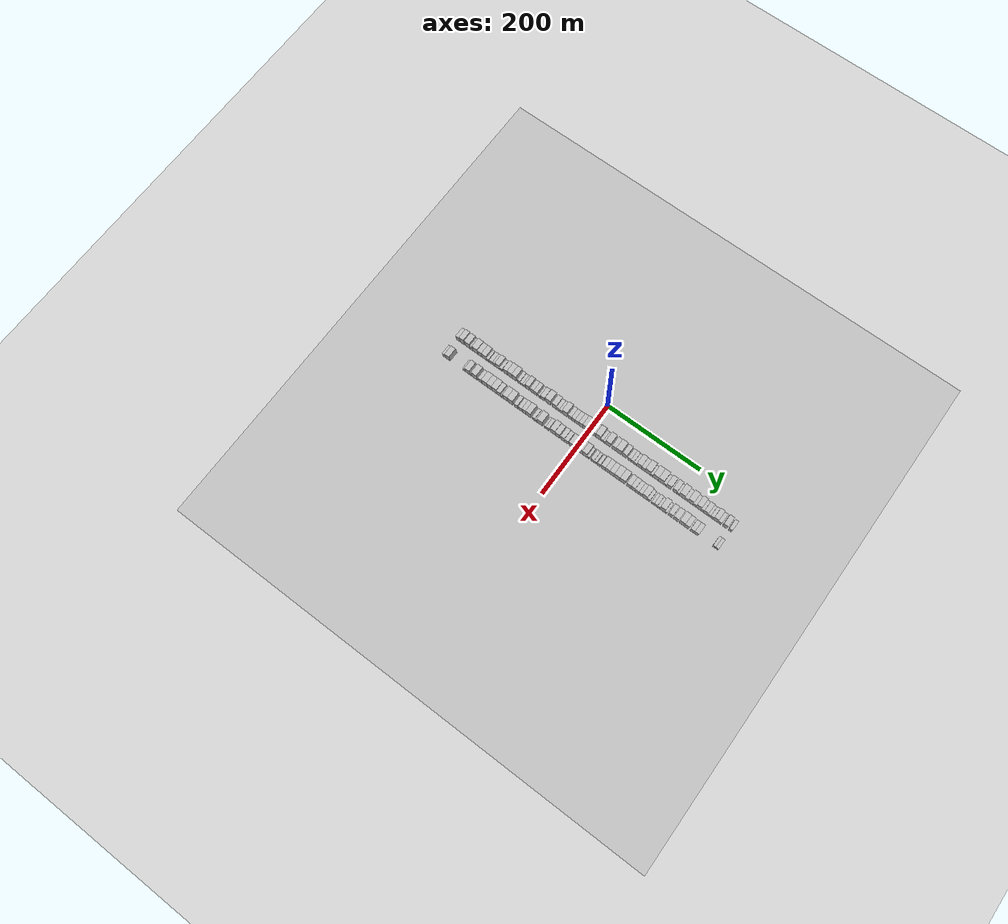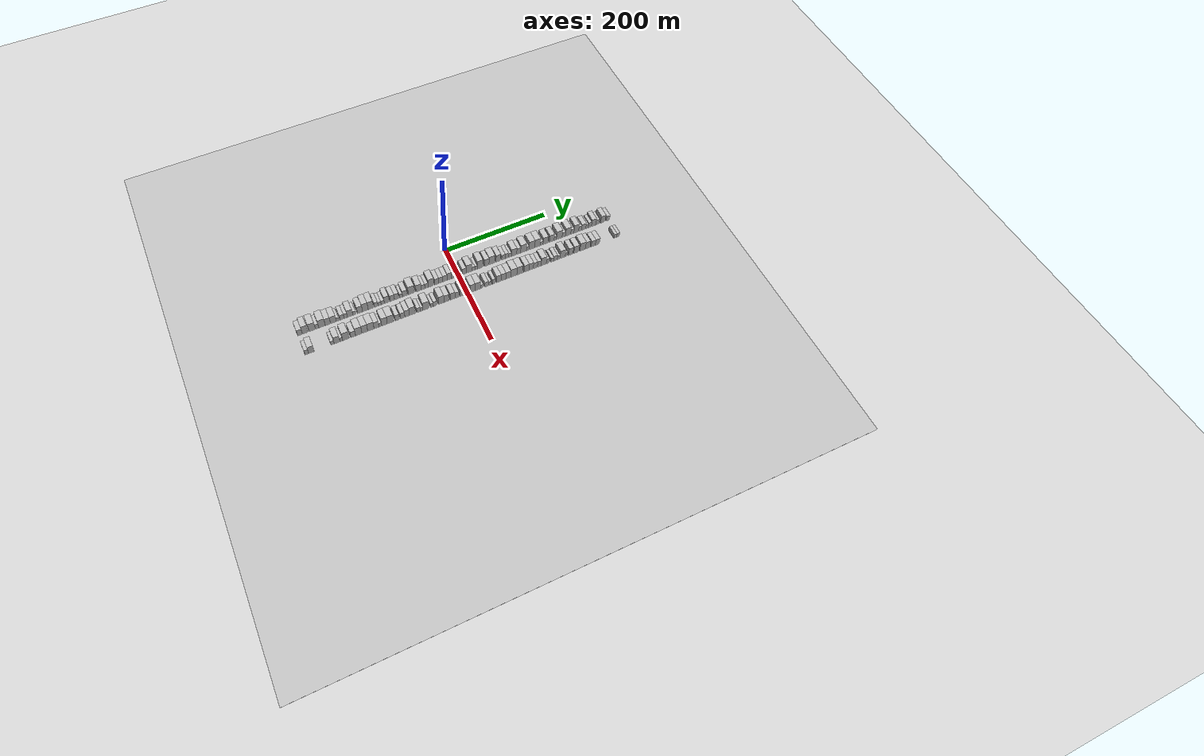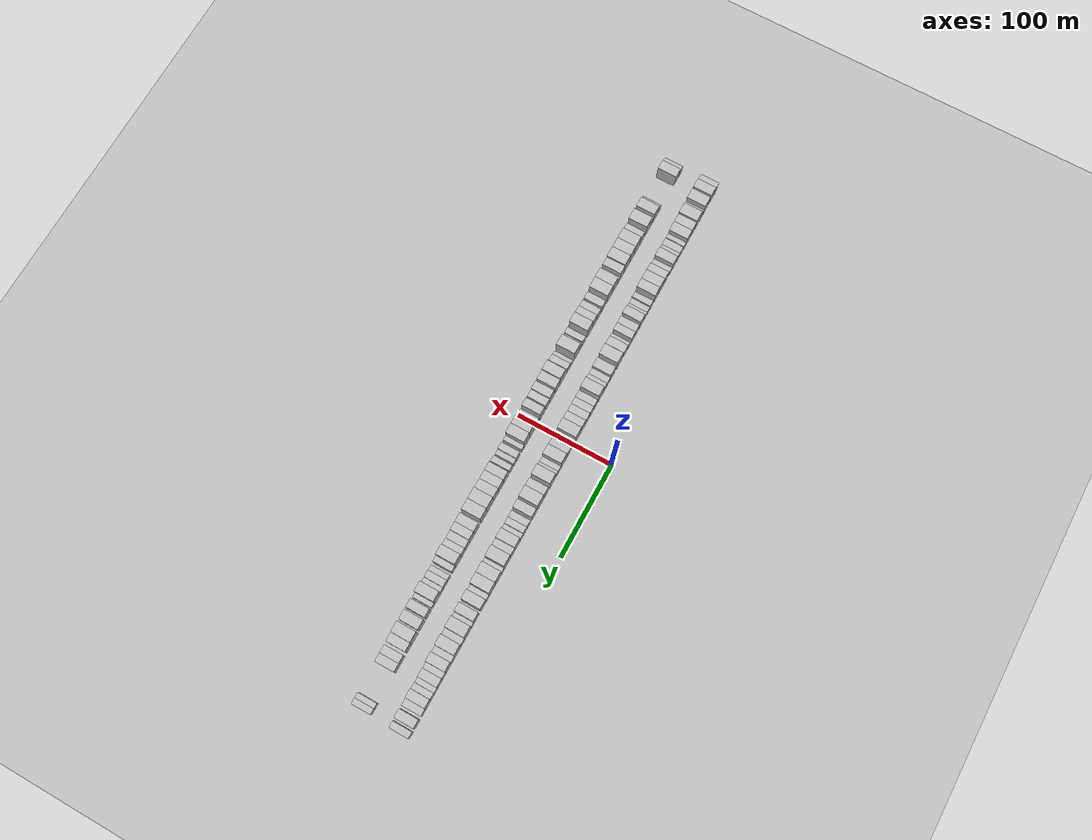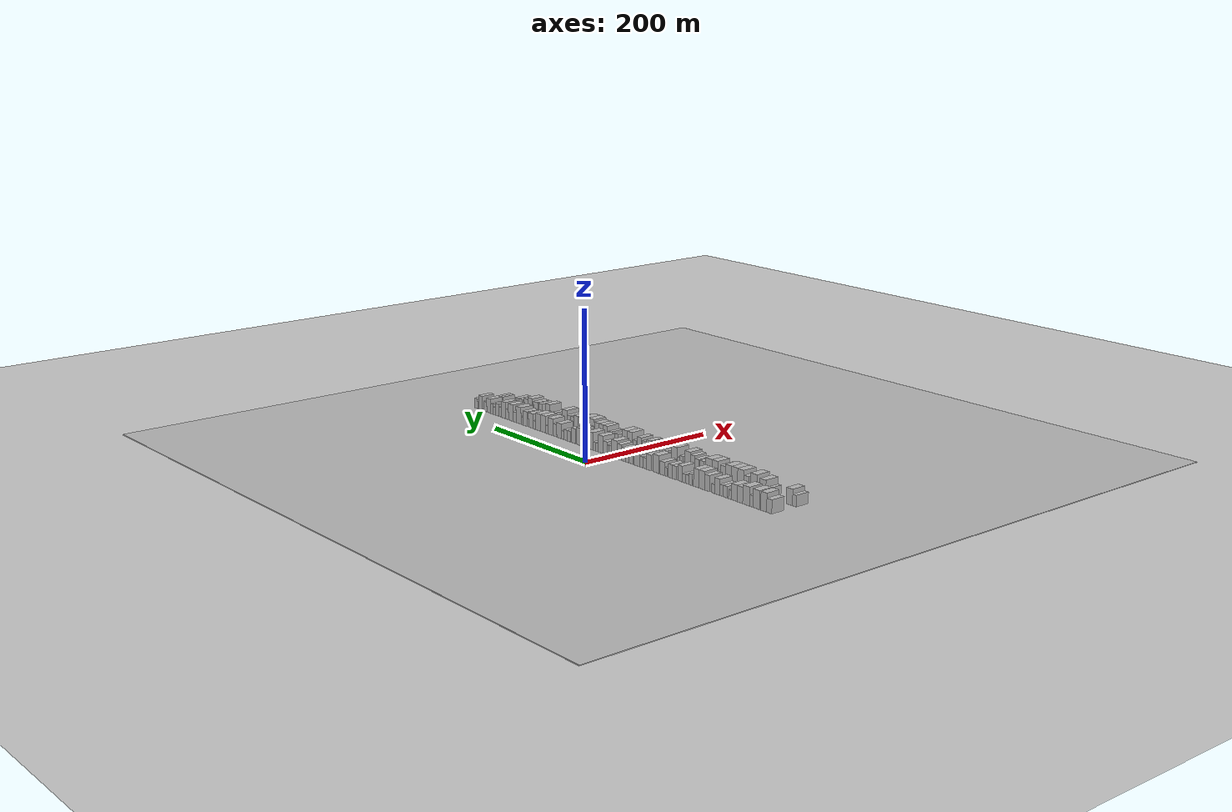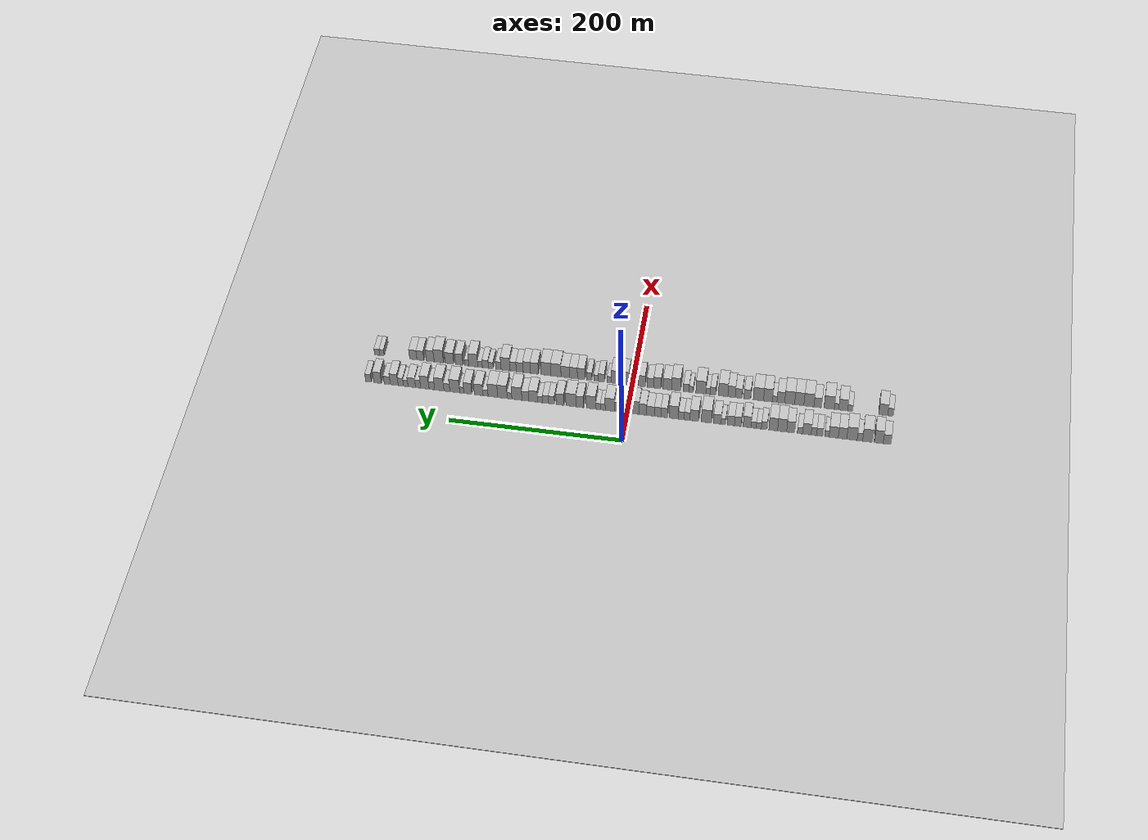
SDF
<?xml version="1.0" encoding="utf-8"?>

<sdf version="1.6">

   <world name="default">

      <gui fullscreen="0">

         <camera name="user_camera">

            <pose>-15 0 4.57585 0 0 0</pose>

            <view_controller>orbit</view_controller>

         </camera>

      </gui>

      <scene>

         <sky>

           <clouds>

             <speed>12</speed>

           </clouds>

         </sky>

         <ambient>0.4 0.4 0.4 1</ambient>

         <background>0.7 0.7 0.7 1</background>

         <shadows>1</shadows>

      </scene>

      <gravity>0 0 -9.8066</gravity>

      <magnetic_field>6e-06 2.3e-05 -4.2e-05</magnetic_field>

      <physics default="0" name="default_physics" type="ode">

         <ode>

            <solver>

               <type>quick</type>

               <iters>10</iters>

               <sor>1.0</sor>

               <use_dynamic_moi_rescaling>0</use_dynamic_moi_rescaling>

            </solver>

            <constraints>

               <cfm>0</cfm>

               <erp>0.2</erp>

               <contact_max_correcting_vel>100</contact_max_correcting_vel>

               <contact_surface_layer>0.001</contact_surface_layer>

            </constraints>

         </ode>

         <max_step_size>0.004</max_step_size>

         <real_time_factor>1</real_time_factor>

         <real_time_update_rate>250</real_time_update_rate>

      </physics>

      <light name="sun" type="directional">

         <cast_shadows>1</cast_shadows>

         <pose>0 0 10 0 0 0</pose>

         <diffuse>0.8 0.8 0.8 1</diffuse>

         <specular>0.2 0.2 0.2 1</specular>

         <attenuation>

            <range>1000</range>

            <constant>0.9</constant>

            <linear>0.01</linear>

            <quadratic>0.001</quadratic>

         </attenuation>

         <direction>-0.5 0.1 -0.9</direction>

      </light>

      <include>

         <name>ground_plane_1</name>

         <uri>model://HANNAS_ground_plane</uri>

         <pose>0 0 0  0 0 0</pose>

      </include>

      <include>

         <name>ground_plane_2</name>

         <uri>model://HANNAS_ground_plane</uri>

         <pose>100 0 0  0 0 0</pose>

      </include>

      <model name="building_1">

         <static>1</static>

         <pose frame="">50.0000 -295.6604 0 0.000000 0.000000 0.000000</pose>

         <link name="link">

            <pose frame="">0 0 9.00 0 0 0</pose>

            <collision name="collision">

               <geometry>

                  <box>

                     <size>20.0000 8.6792 18.0000</size>

                  </box>

               </geometry>

               <max_contacts>10</max_contacts>

               <surface>

                  <contact>

                     <ode/>

                  </contact>

                  <bounce/>

                  <friction>

                     <torsional>

                        <ode/>

                     </torsional>

                     <ode/>

                  </friction>

               </surface>

            </collision>

            <visual name="visual">

               <cast_shadows>0</cast_shadows>

               <geometry>

                  <box>

                     <size>20.0000 8.6792 18.0000</size>

                  </box>

               </geometry>

               <material>

                  <script>

                     <uri>model://HANNAS_wall/materials/scripts</uri>

                     <uri>model://HANNAS_wall/materials/textures</uri>

                     <name>vrc/HANNAS_wall</name>

                  </script>

               </material>

            </visual>

            <self_collide>0</self_collide>

            <enable_wind>0</enable_wind>

            <kinematic>0</kinematic>

         </link>

      </model>

      <model name="building_2">

         <static>1</static>

         <pose frame="">50.0000 -286.3089 0 0.000000 0.000000 0.000000</pose>

         <link name="link">

            <pose frame="">0 0 12.00 0 0 0</pose>

            <collision name="collision">

               <geometry>

                  <box>

                     <size>20.0000 10.0237 24.0000</size>

                  </box>

               </geometry>

               <max_contacts>10</max_contacts>

               <surface>

                  <contact>

                     <ode/>

                  </contact>

                  <bounce/>

                  <friction>

                     <torsional>

                        <ode/>

                     </torsional>

                     <ode/>

                  </friction>

               </surface>

            </collision>

            <visual name="visual">

               <cast_shadows>0</cast_shadows>

               <geometry>

                  <box>

                     <size>20.0000 10.0237 24.0000</size>

                  </box>

               </geometry>

               <material>

                  <script>

                     <uri>model://HANNAS_wall/materials/scripts</uri>

                     <uri>model://HANNAS_wall/materials/textures</uri>

                     <name>vrc/HANNAS_wall</name>

                  </script>

               </material>

            </visual>

            <self_collide>0</self_collide>

            <enable_wind>0</enable_wind>

            <kinematic>0</kinematic>

         </link>

      </model>

      <model name="building_3">

         <static>1</static>

         <pose frame="">50.0000 -273.6609 0 0.000000 0.000000 0.000000</pose>

         <link name="link">

            <pose frame="">0 0 12.00 0 0 0</pose>

            <collision name="collision">

               <geometry>

                  <box>

                     <size>20.0000 11.2724 24.0000</size>

                  </box>

               </geometry>

               <max_contacts>10</max_contacts>

               <surface>

                  <contact>

                     <ode/>

                  </contact>

                  <bounce/>

                  <friction>

                     <torsional>

                        <ode/>

                     </torsional>

                     <ode/>

                  </friction>

               </surface>

            </collision>

            <visual name="visual">

               <cast_shadows>0</cast_shadows>

               <geometry>

                  <box>

                     <size>20.0000 11.2724 24.0000</size>

                  </box>

               </geometry>

               <material>

                  <script>

                     <uri>model://HANNAS_wall/materials/scripts</uri>

                     <uri>model://HANNAS_wall/materials/textures</uri>

                     <name>vrc/HANNAS_wall</name>

                  </script>

               </material>

            </visual>

            <self_collide>0</self_collide>

            <enable_wind>0</enable_wind>

            <kinematic>0</kinematic>

         </link>

      </model>

      <model name="building_4">

         <static>1</static>

         <pose frame="">50.0000 -264.9814 0 0.000000 0.000000 0.000000</pose>

         <link name="link">

            <pose frame="">0 0 7.50 0 0 0</pose>

            <collision name="collision">

               <geometry>

                  <box>

                     <size>20.0000 6.0866 15.0000</size>

                  </box>

               </geometry>

               <max_contacts>10</max_contacts>

               <surface>

                  <contact>

                     <ode/>

                  </contact>

                  <bounce/>

                  <friction>

                     <torsional>

                        <ode/>

                     </torsional>

                     <ode/>

                  </friction>

               </surface>

            </collision>

            <visual name="visual">

               <cast_shadows>0</cast_shadows>

               <geometry>

                  <box>

                     <size>20.0000 6.0866 15.0000</size>

                  </box>

               </geometry>

               <material>

                  <script>

                     <uri>model://HANNAS_wall/materials/scripts</uri>

                     <uri>model://HANNAS_wall/materials/textures</uri>

                     <name>vrc/HANNAS_wall</name>

                  </script>

               </material>

            </visual>

            <self_collide>0</self_collide>

            <enable_wind>0</enable_wind>

            <kinematic>0</kinematic>

         </link>

      </model>

      <model name="building_5">

         <static>1</static>

         <pose frame="">50.0000 -256.0350 0 0.000000 0.000000 0.000000</pose>

         <link name="link">

            <pose frame="">0 0 12.00 0 0 0</pose>

            <collision name="collision">

               <geometry>

                  <box>

                     <size>20.0000 11.8062 24.0000</size>

                  </box>

               </geometry>

               <max_contacts>10</max_contacts>

               <surface>

                  <contact>

                     <ode/>

                  </contact>

                  <bounce/>

                  <friction>

                     <torsional>

                        <ode/>

                     </torsional>

                     <ode/>

                  </friction>

               </surface>

            </collision>

            <visual name="visual">

               <cast_shadows>0</cast_shadows>

               <geometry>

                  <box>

                     <size>20.0000 11.8062 24.0000</size>

                  </box>

               </geometry>

               <material>

                  <script>

                     <uri>model://HANNAS_wall/materials/scripts</uri>

                     <uri>model://HANNAS_wall/materials/textures</uri>

                     <name>vrc/HANNAS_wall</name>

                  </script>

               </material>

            </visual>

            <self_collide>0</self_collide>

            <enable_wind>0</enable_wind>

            <kinematic>0</kinematic>

         </link>

      </model>

      <model name="building_6">

         <static>1</static>

         <pose frame="">50.0000 -245.3482 0 0.000000 0.000000 0.000000</pose>

         <link name="link">

            <pose frame="">0 0 10.50 0 0 0</pose>

            <collision name="collision">

               <geometry>

                  <box>

                     <size>20.0000 9.5675 21.0000</size>

                  </box>

               </geometry>

               <max_contacts>10</max_contacts>

               <surface>

                  <contact>

                     <ode/>

                  </contact>

                  <bounce/>

                  <friction>

                     <torsional>

                        <ode/>

                     </torsional>

                     <ode/>

                  </friction>

               </surface>

            </collision>

            <visual name="visual">

               <cast_shadows>0</cast_shadows>

               <geometry>

                  <box>

                     <size>20.0000 9.5675 21.0000</size>

                  </box>

               </geometry>

               <material>

                  <script>

                     <uri>model://HANNAS_wall/materials/scripts</uri>

                     <uri>model://HANNAS_wall/materials/textures</uri>

                     <name>vrc/HANNAS_wall</name>

                  </script>

               </material>

            </visual>

            <self_collide>0</self_collide>

            <enable_wind>0</enable_wind>

            <kinematic>0</kinematic>

         </link>

      </model>

      <model name="building_7">

         <static>1</static>

         <pose frame="">50.0000 -235.3438 0 0.000000 0.000000 0.000000</pose>

         <link name="link">

            <pose frame="">0 0 10.50 0 0 0</pose>

            <collision name="collision">

               <geometry>

                  <box>

                     <size>20.0000 10.4414 21.0000</size>

                  </box>

               </geometry>

               <max_contacts>10</max_contacts>

               <surface>

                  <contact>

                     <ode/>

                  </contact>

                  <bounce/>

                  <friction>

                     <torsional>

                        <ode/>

                     </torsional>

                     <ode/>

                  </friction>

               </surface>

            </collision>

            <visual name="visual">

               <cast_shadows>0</cast_shadows>

               <geometry>

                  <box>

                     <size>20.0000 10.4414 21.0000</size>

                  </box>

               </geometry>

               <material>

                  <script>

                     <uri>model://HANNAS_wall/materials/scripts</uri>

                     <uri>model://HANNAS_wall/materials/textures</uri>

                     <name>vrc/HANNAS_wall</name>

                  </script>

               </material>

            </visual>

            <self_collide>0</self_collide>

            <enable_wind>0</enable_wind>

            <kinematic>0</kinematic>

         </link>

      </model>

      <model name="building_8">

         <static>1</static>

         <pose frame="">50.0000 -227.6628 0 0.000000 0.000000 0.000000</pose>

         <link name="link">

            <pose frame="">0 0 6.00 0 0 0</pose>

            <collision name="collision">

               <geometry>

                  <box>

                     <size>20.0000 4.9206 12.0000</size>

                  </box>

               </geometry>

               <max_contacts>10</max_contacts>

               <surface>

                  <contact>

                     <ode/>

                  </contact>

                  <bounce/>

                  <friction>

                     <torsional>

                        <ode/>

                     </torsional>

                     <ode/>

                  </friction>

               </surface>

            </collision>

            <visual name="visual">

               <cast_shadows>0</cast_shadows>

               <geometry>

                  <box>

                     <size>20.0000 4.9206 12.0000</size>

                  </box>

               </geometry>

               <material>

                  <script>

                     <uri>model://HANNAS_wall/materials/scripts</uri>

                     <uri>model://HANNAS_wall/materials/textures</uri>

                     <name>vrc/HANNAS_wall</name>

                  </script>

               </material>

            </visual>

            <self_collide>0</self_collide>

            <enable_wind>0</enable_wind>

            <kinematic>0</kinematic>

         </link>

      </model>

      <model name="building_9">

         <static>1</static>

         <pose frame="">50.0000 -219.5754 0 0.000000 0.000000 0.000000</pose>

         <link name="link">

            <pose frame="">0 0 7.50 0 0 0</pose>

            <collision name="collision">

               <geometry>

                  <box>

                     <size>20.0000 7.2541 15.0000</size>

                  </box>

               </geometry>

               <max_contacts>10</max_contacts>

               <surface>

                  <contact>

                     <ode/>

                  </contact>

                  <bounce/>

                  <friction>

                     <torsional>

                        <ode/>

                     </torsional>

                     <ode/>

                  </friction>

               </surface>

            </collision>

            <visual name="visual">

               <cast_shadows>0</cast_shadows>

               <geometry>

                  <box>

                     <size>20.0000 7.2541 15.0000</size>

                  </box>

               </geometry>

               <material>

                  <script>

                     <uri>model://HANNAS_wall/materials/scripts</uri>

                     <uri>model://HANNAS_wall/materials/textures</uri>

                     <name>vrc/HANNAS_wall</name>

                  </script>

               </material>

            </visual>

            <self_collide>0</self_collide>

            <enable_wind>0</enable_wind>

            <kinematic>0</kinematic>

         </link>

      </model>

      <model name="building_10">

         <static>1</static>

         <pose frame="">50.0000 -212.8982 0 0.000000 0.000000 0.000000</pose>

         <link name="link">

            <pose frame="">0 0 7.50 0 0 0</pose>

            <collision name="collision">

               <geometry>

                  <box>

                     <size>20.0000 6.1003 15.0000</size>

                  </box>

               </geometry>

               <max_contacts>10</max_contacts>

               <surface>

                  <contact>

                     <ode/>

                  </contact>

                  <bounce/>

                  <friction>

                     <torsional>

                        <ode/>

                     </torsional>

                     <ode/>

                  </friction>

               </surface>

            </collision>

            <visual name="visual">

               <cast_shadows>0</cast_shadows>

               <geometry>

                  <box>

                     <size>20.0000 6.1003 15.0000</size>

                  </box>

               </geometry>

               <material>

                  <script>

                     <uri>model://HANNAS_wall/materials/scripts</uri>

                     <uri>model://HANNAS_wall/materials/textures</uri>

                     <name>vrc/HANNAS_wall</name>

                  </script>

               </material>

            </visual>

            <self_collide>0</self_collide>

            <enable_wind>0</enable_wind>

            <kinematic>0</kinematic>

         </link>

      </model>

      <model name="building_11">

         <static>1</static>

         <pose frame="">50.0000 -204.9200 0 0.000000 0.000000 0.000000</pose>

         <link name="link">

            <pose frame="">0 0 10.50 0 0 0</pose>

            <collision name="collision">

               <geometry>

                  <box>

                     <size>20.0000 9.8560 21.0000</size>

                  </box>

               </geometry>

               <max_contacts>10</max_contacts>

               <surface>

                  <contact>

                     <ode/>

                  </contact>

                  <bounce/>

                  <friction>

                     <torsional>

                        <ode/>

                     </torsional>

                     <ode/>

                  </friction>

               </surface>

            </collision>

            <visual name="visual">

               <cast_shadows>0</cast_shadows>

               <geometry>

                  <box>

                     <size>20.0000 9.8560 21.0000</size>

                  </box>

               </geometry>

               <material>

                  <script>

                     <uri>model://HANNAS_wall/materials/scripts</uri>

                     <uri>model://HANNAS_wall/materials/textures</uri>

                     <name>vrc/HANNAS_wall</name>

                  </script>

               </material>

            </visual>

            <self_collide>0</self_collide>

            <enable_wind>0</enable_wind>

            <kinematic>0</kinematic>

         </link>

      </model>

      <model name="building_12">

         <static>1</static>

         <pose frame="">50.0000 -197.0589 0 0.000000 0.000000 0.000000</pose>

         <link name="link">

            <pose frame="">0 0 6.00 0 0 0</pose>

            <collision name="collision">

               <geometry>

                  <box>

                     <size>20.0000 5.8663 12.0000</size>

                  </box>

               </geometry>

               <max_contacts>10</max_contacts>

               <surface>

                  <contact>

                     <ode/>

                  </contact>

                  <bounce/>

                  <friction>

                     <torsional>

                        <ode/>

                     </torsional>

                     <ode/>

                  </friction>

               </surface>

            </collision>

            <visual name="visual">

               <cast_shadows>0</cast_shadows>

               <geometry>

                  <box>

                     <size>20.0000 5.8663 12.0000</size>

                  </box>

               </geometry>

               <material>

                  <script>

                     <uri>model://HANNAS_wall/materials/scripts</uri>

                     <uri>model://HANNAS_wall/materials/textures</uri>

                     <name>vrc/HANNAS_wall</name>

                  </script>

               </material>

            </visual>

            <self_collide>0</self_collide>

            <enable_wind>0</enable_wind>

            <kinematic>0</kinematic>

         </link>

      </model>

      <model name="building_13">

         <static>1</static>

         <pose frame="">50.0000 -186.5327 0 0.000000 0.000000 0.000000</pose>

         <link name="link">

            <pose frame="">0 0 10.50 0 0 0</pose>

            <collision name="collision">

               <geometry>

                  <box>

                     <size>20.0000 9.1861 21.0000</size>

                  </box>

               </geometry>

               <max_contacts>10</max_contacts>

               <surface>

                  <contact>

                     <ode/>

                  </contact>

                  <bounce/>

                  <friction>

                     <torsional>

                        <ode/>

                     </torsional>

                     <ode/>

                  </friction>

               </surface>

            </collision>

            <visual name="visual">

               <cast_shadows>0</cast_shadows>

               <geometry>

                  <box>

                     <size>20.0000 9.1861 21.0000</size>

                  </box>

               </geometry>

               <material>

                  <script>

                     <uri>model://HANNAS_wall/materials/scripts</uri>

                     <uri>model://HANNAS_wall/materials/textures</uri>

                     <name>vrc/HANNAS_wall</name>

                  </script>

               </material>

            </visual>

            <self_collide>0</self_collide>

            <enable_wind>0</enable_wind>

            <kinematic>0</kinematic>

         </link>

      </model>

      <model name="building_14">

         <static>1</static>

         <pose frame="">50.0000 -176.8102 0 0.000000 0.000000 0.000000</pose>

         <link name="link">

            <pose frame="">0 0 12.00 0 0 0</pose>

            <collision name="collision">

               <geometry>

                  <box>

                     <size>20.0000 10.2588 24.0000</size>

                  </box>

               </geometry>

               <max_contacts>10</max_contacts>

               <surface>

                  <contact>

                     <ode/>

                  </contact>

                  <bounce/>

                  <friction>

                     <torsional>

                        <ode/>

                     </torsional>

                     <ode/>

                  </friction>

               </surface>

            </collision>

            <visual name="visual">

               <cast_shadows>0</cast_shadows>

               <geometry>

                  <box>

                     <size>20.0000 10.2588 24.0000</size>

                  </box>

               </geometry>

               <material>

                  <script>

                     <uri>model://HANNAS_wall/materials/scripts</uri>

                     <uri>model://HANNAS_wall/materials/textures</uri>

                     <name>vrc/HANNAS_wall</name>

                  </script>

               </material>

            </visual>

            <self_collide>0</self_collide>

            <enable_wind>0</enable_wind>

            <kinematic>0</kinematic>

         </link>

      </model>

      <model name="building_15">

         <static>1</static>

         <pose frame="">50.0000 -166.6893 0 0.000000 0.000000 0.000000</pose>

         <link name="link">

            <pose frame="">0 0 12.00 0 0 0</pose>

            <collision name="collision">

               <geometry>

                  <box>

                     <size>20.0000 9.9830 24.0000</size>

                  </box>

               </geometry>

               <max_contacts>10</max_contacts>

               <surface>

                  <contact>

                     <ode/>

                  </contact>

                  <bounce/>

                  <friction>

                     <torsional>

                        <ode/>

                     </torsional>

                     <ode/>

                  </friction>

               </surface>

            </collision>

            <visual name="visual">

               <cast_shadows>0</cast_shadows>

               <geometry>

                  <box>

                     <size>20.0000 9.9830 24.0000</size>

                  </box>

               </geometry>

               <material>

                  <script>

                     <uri>model://HANNAS_wall/materials/scripts</uri>

                     <uri>model://HANNAS_wall/materials/textures</uri>

                     <name>vrc/HANNAS_wall</name>

                  </script>

               </material>

            </visual>

            <self_collide>0</self_collide>

            <enable_wind>0</enable_wind>

            <kinematic>0</kinematic>

         </link>

      </model>

      <model name="building_16">

         <static>1</static>

         <pose frame="">50.0000 -156.4822 0 0.000000 0.000000 0.000000</pose>

         <link name="link">

            <pose frame="">0 0 7.50 0 0 0</pose>

            <collision name="collision">

               <geometry>

                  <box>

                     <size>20.0000 6.4312 15.0000</size>

                  </box>

               </geometry>

               <max_contacts>10</max_contacts>

               <surface>

                  <contact>

                     <ode/>

                  </contact>

                  <bounce/>

                  <friction>

                     <torsional>

                        <ode/>

                     </torsional>

                     <ode/>

                  </friction>

               </surface>

            </collision>

            <visual name="visual">

               <cast_shadows>0</cast_shadows>

               <geometry>

                  <box>

                     <size>20.0000 6.4312 15.0000</size>

                  </box>

               </geometry>

               <material>

                  <script>

                     <uri>model://HANNAS_wall/materials/scripts</uri>

                     <uri>model://HANNAS_wall/materials/textures</uri>

                     <name>vrc/HANNAS_wall</name>

                  </script>

               </material>

            </visual>

            <self_collide>0</self_collide>

            <enable_wind>0</enable_wind>

            <kinematic>0</kinematic>

         </link>

      </model>

      <model name="building_17">

         <static>1</static>

         <pose frame="">50.0000 -150.3267 0 0.000000 0.000000 0.000000</pose>

         <link name="link">

            <pose frame="">0 0 6.00 0 0 0</pose>

            <collision name="collision">

               <geometry>

                  <box>

                     <size>20.0000 5.8798 12.0000</size>

                  </box>

               </geometry>

               <max_contacts>10</max_contacts>

               <surface>

                  <contact>

                     <ode/>

                  </contact>

                  <bounce/>

                  <friction>

                     <torsional>

                        <ode/>

                     </torsional>

                     <ode/>

                  </friction>

               </surface>

            </collision>

            <visual name="visual">

               <cast_shadows>0</cast_shadows>

               <geometry>

                  <box>

                     <size>20.0000 5.8798 12.0000</size>

                  </box>

               </geometry>

               <material>

                  <script>

                     <uri>model://HANNAS_wall/materials/scripts</uri>

                     <uri>model://HANNAS_wall/materials/textures</uri>

                     <name>vrc/HANNAS_wall</name>

                  </script>

               </material>

            </visual>

            <self_collide>0</self_collide>

            <enable_wind>0</enable_wind>

            <kinematic>0</kinematic>

         </link>

      </model>

      <model name="building_18">

         <static>1</static>

         <pose frame="">50.0000 -144.3886 0 0.000000 0.000000 0.000000</pose>

         <link name="link">

            <pose frame="">0 0 6.00 0 0 0</pose>

            <collision name="collision">

               <geometry>

                  <box>

                     <size>20.0000 5.9963 12.0000</size>

                  </box>

               </geometry>

               <max_contacts>10</max_contacts>

               <surface>

                  <contact>

                     <ode/>

                  </contact>

                  <bounce/>

                  <friction>

                     <torsional>

                        <ode/>

                     </torsional>

                     <ode/>

                  </friction>

               </surface>

            </collision>

            <visual name="visual">

               <cast_shadows>0</cast_shadows>

               <geometry>

                  <box>

                     <size>20.0000 5.9963 12.0000</size>

                  </box>

               </geometry>

               <material>

                  <script>

                     <uri>model://HANNAS_wall/materials/scripts</uri>

                     <uri>model://HANNAS_wall/materials/textures</uri>

                     <name>vrc/HANNAS_wall</name>

                  </script>

               </material>

            </visual>

            <self_collide>0</self_collide>

            <enable_wind>0</enable_wind>

            <kinematic>0</kinematic>

         </link>

      </model>

      <model name="building_19">

         <static>1</static>

         <pose frame="">50.0000 -136.8716 0 0.000000 0.000000 0.000000</pose>

         <link name="link">

            <pose frame="">0 0 10.50 0 0 0</pose>

            <collision name="collision">

               <geometry>

                  <box>

                     <size>20.0000 9.0378 21.0000</size>

                  </box>

               </geometry>

               <max_contacts>10</max_contacts>

               <surface>

                  <contact>

                     <ode/>

                  </contact>

                  <bounce/>

                  <friction>

                     <torsional>

                        <ode/>

                     </torsional>

                     <ode/>

                  </friction>

               </surface>

            </collision>

            <visual name="visual">

               <cast_shadows>0</cast_shadows>

               <geometry>

                  <box>

                     <size>20.0000 9.0378 21.0000</size>

                  </box>

               </geometry>

               <material>

                  <script>

                     <uri>model://HANNAS_wall/materials/scripts</uri>

                     <uri>model://HANNAS_wall/materials/textures</uri>

                     <name>vrc/HANNAS_wall</name>

                  </script>

               </material>

            </visual>

            <self_collide>0</self_collide>

            <enable_wind>0</enable_wind>

            <kinematic>0</kinematic>

         </link>

      </model>

      <model name="building_20">

         <static>1</static>

         <pose frame="">50.0000 -126.3946 0 0.000000 0.000000 0.000000</pose>

         <link name="link">

            <pose frame="">0 0 9.00 0 0 0</pose>

            <collision name="collision">

               <geometry>

                  <box>

                     <size>20.0000 7.9164 18.0000</size>

                  </box>

               </geometry>

               <max_contacts>10</max_contacts>

               <surface>

                  <contact>

                     <ode/>

                  </contact>

                  <bounce/>

                  <friction>

                     <torsional>

                        <ode/>

                     </torsional>

                     <ode/>

                  </friction>

               </surface>

            </collision>

            <visual name="visual">

               <cast_shadows>0</cast_shadows>

               <geometry>

                  <box>

                     <size>20.0000 7.9164 18.0000</size>

                  </box>

               </geometry>

               <material>

                  <script>

                     <uri>model://HANNAS_wall/materials/scripts</uri>

                     <uri>model://HANNAS_wall/materials/textures</uri>

                     <name>vrc/HANNAS_wall</name>

                  </script>

               </material>

            </visual>

            <self_collide>0</self_collide>

            <enable_wind>0</enable_wind>

            <kinematic>0</kinematic>

         </link>

      </model>

      <model name="building_21">

         <static>1</static>

         <pose frame="">50.0000 -118.3697 0 0.000000 0.000000 0.000000</pose>

         <link name="link">

            <pose frame="">0 0 9.00 0 0 0</pose>

            <collision name="collision">

               <geometry>

                  <box>

                     <size>20.0000 8.1333 18.0000</size>

                  </box>

               </geometry>

               <max_contacts>10</max_contacts>

               <surface>

                  <contact>

                     <ode/>

                  </contact>

                  <bounce/>

                  <friction>

                     <torsional>

                        <ode/>

                     </torsional>

                     <ode/>

                  </friction>

               </surface>

            </collision>

            <visual name="visual">

               <cast_shadows>0</cast_shadows>

               <geometry>

                  <box>

                     <size>20.0000 8.1333 18.0000</size>

                  </box>

               </geometry>

               <material>

                  <script>

                     <uri>model://HANNAS_wall/materials/scripts</uri>

                     <uri>model://HANNAS_wall/materials/textures</uri>

                     <name>vrc/HANNAS_wall</name>

                  </script>

               </material>

            </visual>

            <self_collide>0</self_collide>

            <enable_wind>0</enable_wind>

            <kinematic>0</kinematic>

         </link>

      </model>

      <model name="building_22">

         <static>1</static>

         <pose frame="">50.0000 -109.7680 0 0.000000 0.000000 0.000000</pose>

         <link name="link">

            <pose frame="">0 0 6.00 0 0 0</pose>

            <collision name="collision">

               <geometry>

                  <box>

                     <size>20.0000 5.0701 12.0000</size>

                  </box>

               </geometry>

               <max_contacts>10</max_contacts>

               <surface>

                  <contact>

                     <ode/>

                  </contact>

                  <bounce/>

                  <friction>

                     <torsional>

                        <ode/>

                     </torsional>

                     <ode/>

                  </friction>

               </surface>

            </collision>

            <visual name="visual">

               <cast_shadows>0</cast_shadows>

               <geometry>

                  <box>

                     <size>20.0000 5.0701 12.0000</size>

                  </box>

               </geometry>

               <material>

                  <script>

                     <uri>model://HANNAS_wall/materials/scripts</uri>

                     <uri>model://HANNAS_wall/materials/textures</uri>

                     <name>vrc/HANNAS_wall</name>

                  </script>

               </material>

            </visual>

            <self_collide>0</self_collide>

            <enable_wind>0</enable_wind>

            <kinematic>0</kinematic>

         </link>

      </model>

      <model name="building_23">

         <static>1</static>

         <pose frame="">50.0000 -102.7718 0 0.000000 0.000000 0.000000</pose>

         <link name="link">

            <pose frame="">0 0 9.00 0 0 0</pose>

            <collision name="collision">

               <geometry>

                  <box>

                     <size>20.0000 8.9224 18.0000</size>

                  </box>

               </geometry>

               <max_contacts>10</max_contacts>

               <surface>

                  <contact>

                     <ode/>

                  </contact>

                  <bounce/>

                  <friction>

                     <torsional>

                        <ode/>

                     </torsional>

                     <ode/>

                  </friction>

               </surface>

            </collision>

            <visual name="visual">

               <cast_shadows>0</cast_shadows>

               <geometry>

                  <box>

                     <size>20.0000 8.9224 18.0000</size>

                  </box>

               </geometry>

               <material>

                  <script>

                     <uri>model://HANNAS_wall/materials/scripts</uri>

                     <uri>model://HANNAS_wall/materials/textures</uri>

                     <name>vrc/HANNAS_wall</name>

                  </script>

               </material>

            </visual>

            <self_collide>0</self_collide>

            <enable_wind>0</enable_wind>

            <kinematic>0</kinematic>

         </link>

      </model>

      <model name="building_24">

         <static>1</static>

         <pose frame="">50.0000 -90.4507 0 0.000000 0.000000 0.000000</pose>

         <link name="link">

            <pose frame="">0 0 12.00 0 0 0</pose>

            <collision name="collision">

               <geometry>

                  <box>

                     <size>20.0000 11.7199 24.0000</size>

                  </box>

               </geometry>

               <max_contacts>10</max_contacts>

               <surface>

                  <contact>

                     <ode/>

                  </contact>

                  <bounce/>

                  <friction>

                     <torsional>

                        <ode/>

                     </torsional>

                     <ode/>

                  </friction>

               </surface>

            </collision>

            <visual name="visual">

               <cast_shadows>0</cast_shadows>

               <geometry>

                  <box>

                     <size>20.0000 11.7199 24.0000</size>

                  </box>

               </geometry>

               <material>

                  <script>

                     <uri>model://HANNAS_wall/materials/scripts</uri>

                     <uri>model://HANNAS_wall/materials/textures</uri>

                     <name>vrc/HANNAS_wall</name>

                  </script>

               </material>

            </visual>

            <self_collide>0</self_collide>

            <enable_wind>0</enable_wind>

            <kinematic>0</kinematic>

         </link>

      </model>

      <model name="building_25">

         <static>1</static>

         <pose frame="">50.0000 -76.5439 0 0.000000 0.000000 0.000000</pose>

         <link name="link">

            <pose frame="">0 0 10.50 0 0 0</pose>

            <collision name="collision">

               <geometry>

                  <box>

                     <size>20.0000 10.0936 21.0000</size>

                  </box>

               </geometry>

               <max_contacts>10</max_contacts>

               <surface>

                  <contact>

                     <ode/>

                  </contact>

                  <bounce/>

                  <friction>

                     <torsional>

                        <ode/>

                     </torsional>

                     <ode/>

                  </friction>

               </surface>

            </collision>

            <visual name="visual">

               <cast_shadows>0</cast_shadows>

               <geometry>

                  <box>

                     <size>20.0000 10.0936 21.0000</size>

                  </box>

               </geometry>

               <material>

                  <script>

                     <uri>model://HANNAS_wall/materials/scripts</uri>

                     <uri>model://HANNAS_wall/materials/textures</uri>

                     <name>vrc/HANNAS_wall</name>

                  </script>

               </material>

            </visual>

            <self_collide>0</self_collide>

            <enable_wind>0</enable_wind>

            <kinematic>0</kinematic>

         </link>

      </model>

      <model name="building_26">

         <static>1</static>

         <pose frame="">50.0000 -68.1587 0 0.000000 0.000000 0.000000</pose>

         <link name="link">

            <pose frame="">0 0 7.50 0 0 0</pose>

            <collision name="collision">

               <geometry>

                  <box>

                     <size>20.0000 6.6767 15.0000</size>

                  </box>

               </geometry>

               <max_contacts>10</max_contacts>

               <surface>

                  <contact>

                     <ode/>

                  </contact>

                  <bounce/>

                  <friction>

                     <torsional>

                        <ode/>

                     </torsional>

                     <ode/>

                  </friction>

               </surface>

            </collision>

            <visual name="visual">

               <cast_shadows>0</cast_shadows>

               <geometry>

                  <box>

                     <size>20.0000 6.6767 15.0000</size>

                  </box>

               </geometry>

               <material>

                  <script>

                     <uri>model://HANNAS_wall/materials/scripts</uri>

                     <uri>model://HANNAS_wall/materials/textures</uri>

                     <name>vrc/HANNAS_wall</name>

                  </script>

               </material>

            </visual>

            <self_collide>0</self_collide>

            <enable_wind>0</enable_wind>

            <kinematic>0</kinematic>

         </link>

      </model>

      <model name="building_27">

         <static>1</static>

         <pose frame="">50.0000 -61.5330 0 0.000000 0.000000 0.000000</pose>

         <link name="link">

            <pose frame="">0 0 7.50 0 0 0</pose>

            <collision name="collision">

               <geometry>

                  <box>

                     <size>20.0000 6.5746 15.0000</size>

                  </box>

               </geometry>

               <max_contacts>10</max_contacts>

               <surface>

                  <contact>

                     <ode/>

                  </contact>

                  <bounce/>

                  <friction>

                     <torsional>

                        <ode/>

                     </torsional>

                     <ode/>

                  </friction>

               </surface>

            </collision>

            <visual name="visual">

               <cast_shadows>0</cast_shadows>

               <geometry>

                  <box>

                     <size>20.0000 6.5746 15.0000</size>

                  </box>

               </geometry>

               <material>

                  <script>

                     <uri>model://HANNAS_wall/materials/scripts</uri>

                     <uri>model://HANNAS_wall/materials/textures</uri>

                     <name>vrc/HANNAS_wall</name>

                  </script>

               </material>

            </visual>

            <self_collide>0</self_collide>

            <enable_wind>0</enable_wind>

            <kinematic>0</kinematic>

         </link>

      </model>

      <model name="building_28">

         <static>1</static>

         <pose frame="">50.0000 -52.8710 0 0.000000 0.000000 0.000000</pose>

         <link name="link">

            <pose frame="">0 0 12.00 0 0 0</pose>

            <collision name="collision">

               <geometry>

                  <box>

                     <size>20.0000 10.7494 24.0000</size>

                  </box>

               </geometry>

               <max_contacts>10</max_contacts>

               <surface>

                  <contact>

                     <ode/>

                  </contact>

                  <bounce/>

                  <friction>

                     <torsional>

                        <ode/>

                     </torsional>

                     <ode/>

                  </friction>

               </surface>

            </collision>

            <visual name="visual">

               <cast_shadows>0</cast_shadows>

               <geometry>

                  <box>

                     <size>20.0000 10.7494 24.0000</size>

                  </box>

               </geometry>

               <material>

                  <script>

                     <uri>model://HANNAS_wall/materials/scripts</uri>

                     <uri>model://HANNAS_wall/materials/textures</uri>

                     <name>vrc/HANNAS_wall</name>

                  </script>

               </material>

            </visual>

            <self_collide>0</self_collide>

            <enable_wind>0</enable_wind>

            <kinematic>0</kinematic>

         </link>

      </model>

      <model name="building_29">

         <static>1</static>

         <pose frame="">50.0000 -41.6983 0 0.000000 0.000000 0.000000</pose>

         <link name="link">

            <pose frame="">0 0 9.00 0 0 0</pose>

            <collision name="collision">

               <geometry>

                  <box>

                     <size>20.0000 7.5961 18.0000</size>

                  </box>

               </geometry>

               <max_contacts>10</max_contacts>

               <surface>

                  <contact>

                     <ode/>

                  </contact>

                  <bounce/>

                  <friction>

                     <torsional>

                        <ode/>

                     </torsional>

                     <ode/>

                  </friction>

               </surface>

            </collision>

            <visual name="visual">

               <cast_shadows>0</cast_shadows>

               <geometry>

                  <box>

                     <size>20.0000 7.5961 18.0000</size>

                  </box>

               </geometry>

               <material>

                  <script>

                     <uri>model://HANNAS_wall/materials/scripts</uri>

                     <uri>model://HANNAS_wall/materials/textures</uri>

                     <name>vrc/HANNAS_wall</name>

                  </script>

               </material>

            </visual>

            <self_collide>0</self_collide>

            <enable_wind>0</enable_wind>

            <kinematic>0</kinematic>

         </link>

      </model>

      <model name="building_30">

         <static>1</static>

         <pose frame="">50.0000 -34.1289 0 0.000000 0.000000 0.000000</pose>

         <link name="link">

            <pose frame="">0 0 9.00 0 0 0</pose>

            <collision name="collision">

               <geometry>

                  <box>

                     <size>20.0000 7.5425 18.0000</size>

                  </box>

               </geometry>

               <max_contacts>10</max_contacts>

               <surface>

                  <contact>

                     <ode/>

                  </contact>

                  <bounce/>

                  <friction>

                     <torsional>

                        <ode/>

                     </torsional>

                     <ode/>

                  </friction>

               </surface>

            </collision>

            <visual name="visual">

               <cast_shadows>0</cast_shadows>

               <geometry>

                  <box>

                     <size>20.0000 7.5425 18.0000</size>

                  </box>

               </geometry>

               <material>

                  <script>

                     <uri>model://HANNAS_wall/materials/scripts</uri>

                     <uri>model://HANNAS_wall/materials/textures</uri>

                     <name>vrc/HANNAS_wall</name>

                  </script>

               </material>

            </visual>

            <self_collide>0</self_collide>

            <enable_wind>0</enable_wind>

            <kinematic>0</kinematic>

         </link>

      </model>

      <model name="building_31">

         <static>1</static>

         <pose frame="">50.0000 -26.0431 0 0.000000 0.000000 0.000000</pose>

         <link name="link">

            <pose frame="">0 0 9.00 0 0 0</pose>

            <collision name="collision">

               <geometry>

                  <box>

                     <size>20.0000 8.6293 18.0000</size>

                  </box>

               </geometry>

               <max_contacts>10</max_contacts>

               <surface>

                  <contact>

                     <ode/>

                  </contact>

                  <bounce/>

                  <friction>

                     <torsional>

                        <ode/>

                     </torsional>

                     <ode/>

                  </friction>

               </surface>

            </collision>

            <visual name="visual">

               <cast_shadows>0</cast_shadows>

               <geometry>

                  <box>

                     <size>20.0000 8.6293 18.0000</size>

                  </box>

               </geometry>

               <material>

                  <script>

                     <uri>model://HANNAS_wall/materials/scripts</uri>

                     <uri>model://HANNAS_wall/materials/textures</uri>

                     <name>vrc/HANNAS_wall</name>

                  </script>

               </material>

            </visual>

            <self_collide>0</self_collide>

            <enable_wind>0</enable_wind>

            <kinematic>0</kinematic>

         </link>

      </model>

      <model name="building_32">

         <static>1</static>

         <pose frame="">50.0000 -17.4651 0 0.000000 0.000000 0.000000</pose>

         <link name="link">

            <pose frame="">0 0 10.50 0 0 0</pose>

            <collision name="collision">

               <geometry>

                  <box>

                     <size>20.0000 8.5266 21.0000</size>

                  </box>

               </geometry>

               <max_contacts>10</max_contacts>

               <surface>

                  <contact>

                     <ode/>

                  </contact>

                  <bounce/>

                  <friction>

                     <torsional>

                        <ode/>

                     </torsional>

                     <ode/>

                  </friction>

               </surface>

            </collision>

            <visual name="visual">

               <cast_shadows>0</cast_shadows>

               <geometry>

                  <box>

                     <size>20.0000 8.5266 21.0000</size>

                  </box>

               </geometry>

               <material>

                  <script>

                     <uri>model://HANNAS_wall/materials/scripts</uri>

                     <uri>model://HANNAS_wall/materials/textures</uri>

                     <name>vrc/HANNAS_wall</name>

                  </script>

               </material>

            </visual>

            <self_collide>0</self_collide>

            <enable_wind>0</enable_wind>

            <kinematic>0</kinematic>

         </link>

      </model>

      <model name="building_33">

         <static>1</static>

         <pose frame="">50.0000 -7.6380 0 0.000000 0.000000 0.000000</pose>

         <link name="link">

            <pose frame="">0 0 12.00 0 0 0</pose>

            <collision name="collision">

               <geometry>

                  <box>

                     <size>20.0000 11.1276 24.0000</size>

                  </box>

               </geometry>

               <max_contacts>10</max_contacts>

               <surface>

                  <contact>

                     <ode/>

                  </contact>

                  <bounce/>

                  <friction>

                     <torsional>

                        <ode/>

                     </torsional>

                     <ode/>

                  </friction>

               </surface>

            </collision>

            <visual name="visual">

               <cast_shadows>0</cast_shadows>

               <geometry>

                  <box>

                     <size>20.0000 11.1276 24.0000</size>

                  </box>

               </geometry>

               <material>

                  <script>

                     <uri>model://HANNAS_wall/materials/scripts</uri>

                     <uri>model://HANNAS_wall/materials/textures</uri>

                     <name>vrc/HANNAS_wall</name>

                  </script>

               </material>

            </visual>

            <self_collide>0</self_collide>

            <enable_wind>0</enable_wind>

            <kinematic>0</kinematic>

         </link>

      </model>

      <model name="building_34">

         <static>1</static>

         <pose frame="">50.0000 1.1589 0 0.000000 0.000000 0.000000</pose>

         <link name="link">

            <pose frame="">0 0 7.50 0 0 0</pose>

            <collision name="collision">

               <geometry>

                  <box>

                     <size>20.0000 6.4662 15.0000</size>

                  </box>

               </geometry>

               <max_contacts>10</max_contacts>

               <surface>

                  <contact>

                     <ode/>

                  </contact>

                  <bounce/>

                  <friction>

                     <torsional>

                        <ode/>

                     </torsional>

                     <ode/>

                  </friction>

               </surface>

            </collision>

            <visual name="visual">

               <cast_shadows>0</cast_shadows>

               <geometry>

                  <box>

                     <size>20.0000 6.4662 15.0000</size>

                  </box>

               </geometry>

               <material>

                  <script>

                     <uri>model://HANNAS_wall/materials/scripts</uri>

                     <uri>model://HANNAS_wall/materials/textures</uri>

                     <name>vrc/HANNAS_wall</name>

                  </script>

               </material>

            </visual>

            <self_collide>0</self_collide>

            <enable_wind>0</enable_wind>

            <kinematic>0</kinematic>

         </link>

      </model>

      <model name="building_35">

         <static>1</static>

         <pose frame="">50.0000 11.3959 0 0.000000 0.000000 0.000000</pose>

         <link name="link">

            <pose frame="">0 0 9.00 0 0 0</pose>

            <collision name="collision">

               <geometry>

                  <box>

                     <size>20.0000 8.0078 18.0000</size>

                  </box>

               </geometry>

               <max_contacts>10</max_contacts>

               <surface>

                  <contact>

                     <ode/>

                  </contact>

                  <bounce/>

                  <friction>

                     <torsional>

                        <ode/>

                     </torsional>

                     <ode/>

                  </friction>

               </surface>

            </collision>

            <visual name="visual">

               <cast_shadows>0</cast_shadows>

               <geometry>

                  <box>

                     <size>20.0000 8.0078 18.0000</size>

                  </box>

               </geometry>

               <material>

                  <script>

                     <uri>model://HANNAS_wall/materials/scripts</uri>

                     <uri>model://HANNAS_wall/materials/textures</uri>

                     <name>vrc/HANNAS_wall</name>

                  </script>

               </material>

            </visual>

            <self_collide>0</self_collide>

            <enable_wind>0</enable_wind>

            <kinematic>0</kinematic>

         </link>

      </model>

      <model name="building_36">

         <static>1</static>

         <pose frame="">50.0000 20.8704 0 0.000000 0.000000 0.000000</pose>

         <link name="link">

            <pose frame="">0 0 12.00 0 0 0</pose>

            <collision name="collision">

               <geometry>

                  <box>

                     <size>20.0000 10.9411 24.0000</size>

                  </box>

               </geometry>

               <max_contacts>10</max_contacts>

               <surface>

                  <contact>

                     <ode/>

                  </contact>

                  <bounce/>

                  <friction>

                     <torsional>

                        <ode/>

                     </torsional>

                     <ode/>

                  </friction>

               </surface>

            </collision>

            <visual name="visual">

               <cast_shadows>0</cast_shadows>

               <geometry>

                  <box>

                     <size>20.0000 10.9411 24.0000</size>

                  </box>

               </geometry>

               <material>

                  <script>

                     <uri>model://HANNAS_wall/materials/scripts</uri>

                     <uri>model://HANNAS_wall/materials/textures</uri>

                     <name>vrc/HANNAS_wall</name>

                  </script>

               </material>

            </visual>

            <self_collide>0</self_collide>

            <enable_wind>0</enable_wind>

            <kinematic>0</kinematic>

         </link>

      </model>

      <model name="building_37">

         <static>1</static>

         <pose frame="">50.0000 29.1648 0 0.000000 0.000000 0.000000</pose>

         <link name="link">

            <pose frame="">0 0 6.00 0 0 0</pose>

            <collision name="collision">

               <geometry>

                  <box>

                     <size>20.0000 5.6477 12.0000</size>

                  </box>

               </geometry>

               <max_contacts>10</max_contacts>

               <surface>

                  <contact>

                     <ode/>

                  </contact>

                  <bounce/>

                  <friction>

                     <torsional>

                        <ode/>

                     </torsional>

                     <ode/>

                  </friction>

               </surface>

            </collision>

            <visual name="visual">

               <cast_shadows>0</cast_shadows>

               <geometry>

                  <box>

                     <size>20.0000 5.6477 12.0000</size>

                  </box>

               </geometry>

               <material>

                  <script>

                     <uri>model://HANNAS_wall/materials/scripts</uri>

                     <uri>model://HANNAS_wall/materials/textures</uri>

                     <name>vrc/HANNAS_wall</name>

                  </script>

               </material>

            </visual>

            <self_collide>0</self_collide>

            <enable_wind>0</enable_wind>

            <kinematic>0</kinematic>

         </link>

      </model>

      <model name="building_38">

         <static>1</static>

         <pose frame="">50.0000 34.5339 0 0.000000 0.000000 0.000000</pose>

         <link name="link">

            <pose frame="">0 0 6.00 0 0 0</pose>

            <collision name="collision">

               <geometry>

                  <box>

                     <size>20.0000 5.0903 12.0000</size>

                  </box>

               </geometry>

               <max_contacts>10</max_contacts>

               <surface>

                  <contact>

                     <ode/>

                  </contact>

                  <bounce/>

                  <friction>

                     <torsional>

                        <ode/>

                     </torsional>

                     <ode/>

                  </friction>

               </surface>

            </collision>

            <visual name="visual">

               <cast_shadows>0</cast_shadows>

               <geometry>

                  <box>

                     <size>20.0000 5.0903 12.0000</size>

                  </box>

               </geometry>

               <material>

                  <script>

                     <uri>model://HANNAS_wall/materials/scripts</uri>

                     <uri>model://HANNAS_wall/materials/textures</uri>

                     <name>vrc/HANNAS_wall</name>

                  </script>

               </material>

            </visual>

            <self_collide>0</self_collide>

            <enable_wind>0</enable_wind>

            <kinematic>0</kinematic>

         </link>

      </model>

      <model name="building_39">

         <static>1</static>

         <pose frame="">50.0000 42.5966 0 0.000000 0.000000 0.000000</pose>

         <link name="link">

            <pose frame="">0 0 12.00 0 0 0</pose>

            <collision name="collision">

               <geometry>

                  <box>

                     <size>20.0000 11.0351 24.0000</size>

                  </box>

               </geometry>

               <max_contacts>10</max_contacts>

               <surface>

                  <contact>

                     <ode/>

                  </contact>

                  <bounce/>

                  <friction>

                     <torsional>

                        <ode/>

                     </torsional>

                     <ode/>

                  </friction>

               </surface>

            </collision>

            <visual name="visual">

               <cast_shadows>0</cast_shadows>

               <geometry>

                  <box>

                     <size>20.0000 11.0351 24.0000</size>

                  </box>

               </geometry>

               <material>

                  <script>

                     <uri>model://HANNAS_wall/materials/scripts</uri>

                     <uri>model://HANNAS_wall/materials/textures</uri>

                     <name>vrc/HANNAS_wall</name>

                  </script>

               </material>

            </visual>

            <self_collide>0</self_collide>

            <enable_wind>0</enable_wind>

            <kinematic>0</kinematic>

         </link>

      </model>

      <model name="building_40">

         <static>1</static>

         <pose frame="">50.0000 55.5203 0 0.000000 0.000000 0.000000</pose>

         <link name="link">

            <pose frame="">0 0 10.50 0 0 0</pose>

            <collision name="collision">

               <geometry>

                  <box>

                     <size>20.0000 8.8122 21.0000</size>

                  </box>

               </geometry>

               <max_contacts>10</max_contacts>

               <surface>

                  <contact>

                     <ode/>

                  </contact>

                  <bounce/>

                  <friction>

                     <torsional>

                        <ode/>

                     </torsional>

                     <ode/>

                  </friction>

               </surface>

            </collision>

            <visual name="visual">

               <cast_shadows>0</cast_shadows>

               <geometry>

                  <box>

                     <size>20.0000 8.8122 21.0000</size>

                  </box>

               </geometry>

               <material>

                  <script>

                     <uri>model://HANNAS_wall/materials/scripts</uri>

                     <uri>model://HANNAS_wall/materials/textures</uri>

                     <name>vrc/HANNAS_wall</name>

                  </script>

               </material>

            </visual>

            <self_collide>0</self_collide>

            <enable_wind>0</enable_wind>

            <kinematic>0</kinematic>

         </link>

      </model>

      <model name="building_41">

         <static>1</static>

         <pose frame="">50.0000 65.8986 0 0.000000 0.000000 0.000000</pose>

         <link name="link">

            <pose frame="">0 0 12.00 0 0 0</pose>

            <collision name="collision">

               <geometry>

                  <box>

                     <size>20.0000 11.9445 24.0000</size>

                  </box>

               </geometry>

               <max_contacts>10</max_contacts>

               <surface>

                  <contact>

                     <ode/>

                  </contact>

                  <bounce/>

                  <friction>

                     <torsional>

                        <ode/>

                     </torsional>

                     <ode/>

                  </friction>

               </surface>

            </collision>

            <visual name="visual">

               <cast_shadows>0</cast_shadows>

               <geometry>

                  <box>

                     <size>20.0000 11.9445 24.0000</size>

                  </box>

               </geometry>

               <material>

                  <script>

                     <uri>model://HANNAS_wall/materials/scripts</uri>

                     <uri>model://HANNAS_wall/materials/textures</uri>

                     <name>vrc/HANNAS_wall</name>

                  </script>

               </material>

            </visual>

            <self_collide>0</self_collide>

            <enable_wind>0</enable_wind>

            <kinematic>0</kinematic>

         </link>

      </model>

      <model name="building_42">

         <static>1</static>

         <pose frame="">50.0000 78.4836 0 0.000000 0.000000 0.000000</pose>

         <link name="link">

            <pose frame="">0 0 10.50 0 0 0</pose>

            <collision name="collision">

               <geometry>

                  <box>

                     <size>20.0000 9.2255 21.0000</size>

                  </box>

               </geometry>

               <max_contacts>10</max_contacts>

               <surface>

                  <contact>

                     <ode/>

                  </contact>

                  <bounce/>

                  <friction>

                     <torsional>

                        <ode/>

                     </torsional>

                     <ode/>

                  </friction>

               </surface>

            </collision>

            <visual name="visual">

               <cast_shadows>0</cast_shadows>

               <geometry>

                  <box>

                     <size>20.0000 9.2255 21.0000</size>

                  </box>

               </geometry>

               <material>

                  <script>

                     <uri>model://HANNAS_wall/materials/scripts</uri>

                     <uri>model://HANNAS_wall/materials/textures</uri>

                     <name>vrc/HANNAS_wall</name>

                  </script>

               </material>

            </visual>

            <self_collide>0</self_collide>

            <enable_wind>0</enable_wind>

            <kinematic>0</kinematic>

         </link>

      </model>

      <model name="building_43">

         <static>1</static>

         <pose frame="">50.0000 88.6178 0 0.000000 0.000000 0.000000</pose>

         <link name="link">

            <pose frame="">0 0 7.50 0 0 0</pose>

            <collision name="collision">

               <geometry>

                  <box>

                     <size>20.0000 7.0429 15.0000</size>

                  </box>

               </geometry>

               <max_contacts>10</max_contacts>

               <surface>

                  <contact>

                     <ode/>

                  </contact>

                  <bounce/>

                  <friction>

                     <torsional>

                        <ode/>

                     </torsional>

                     <ode/>

                  </friction>

               </surface>

            </collision>

            <visual name="visual">

               <cast_shadows>0</cast_shadows>

               <geometry>

                  <box>

                     <size>20.0000 7.0429 15.0000</size>

                  </box>

               </geometry>

               <material>

                  <script>

                     <uri>model://HANNAS_wall/materials/scripts</uri>

                     <uri>model://HANNAS_wall/materials/textures</uri>

                     <name>vrc/HANNAS_wall</name>

                  </script>

               </material>

            </visual>

            <self_collide>0</self_collide>

            <enable_wind>0</enable_wind>

            <kinematic>0</kinematic>

         </link>

      </model>

      <model name="building_44">

         <static>1</static>

         <pose frame="">50.0000 95.4951 0 0.000000 0.000000 0.000000</pose>

         <link name="link">

            <pose frame="">0 0 7.50 0 0 0</pose>

            <collision name="collision">

               <geometry>

                  <box>

                     <size>20.0000 6.7116 15.0000</size>

                  </box>

               </geometry>

               <max_contacts>10</max_contacts>

               <surface>

                  <contact>

                     <ode/>

                  </contact>

                  <bounce/>

                  <friction>

                     <torsional>

                        <ode/>

                     </torsional>

                     <ode/>

                  </friction>

               </surface>

            </collision>

            <visual name="visual">

               <cast_shadows>0</cast_shadows>

               <geometry>

                  <box>

                     <size>20.0000 6.7116 15.0000</size>

                  </box>

               </geometry>

               <material>

                  <script>

                     <uri>model://HANNAS_wall/materials/scripts</uri>

                     <uri>model://HANNAS_wall/materials/textures</uri>

                     <name>vrc/HANNAS_wall</name>

                  </script>

               </material>

            </visual>

            <self_collide>0</self_collide>

            <enable_wind>0</enable_wind>

            <kinematic>0</kinematic>

         </link>

      </model>

      <model name="building_45">

         <static>1</static>

         <pose frame="">50.0000 101.7632 0 0.000000 0.000000 0.000000</pose>

         <link name="link">

            <pose frame="">0 0 6.00 0 0 0</pose>

            <collision name="collision">

               <geometry>

                  <box>

                     <size>20.0000 5.8247 12.0000</size>

                  </box>

               </geometry>

               <max_contacts>10</max_contacts>

               <surface>

                  <contact>

                     <ode/>

                  </contact>

                  <bounce/>

                  <friction>

                     <torsional>

                        <ode/>

                     </torsional>

                     <ode/>

                  </friction>

               </surface>

            </collision>

            <visual name="visual">

               <cast_shadows>0</cast_shadows>

               <geometry>

                  <box>

                     <size>20.0000 5.8247 12.0000</size>

                  </box>

               </geometry>

               <material>

                  <script>

                     <uri>model://HANNAS_wall/materials/scripts</uri>

                     <uri>model://HANNAS_wall/materials/textures</uri>

                     <name>vrc/HANNAS_wall</name>

                  </script>

               </material>

            </visual>

            <self_collide>0</self_collide>

            <enable_wind>0</enable_wind>

            <kinematic>0</kinematic>

         </link>

      </model>

      <model name="building_46">

         <static>1</static>

         <pose frame="">50.0000 109.8124 0 0.000000 0.000000 0.000000</pose>

         <link name="link">

            <pose frame="">0 0 10.50 0 0 0</pose>

            <collision name="collision">

               <geometry>

                  <box>

                     <size>20.0000 10.2737 21.0000</size>

                  </box>

               </geometry>

               <max_contacts>10</max_contacts>

               <surface>

                  <contact>

                     <ode/>

                  </contact>

                  <bounce/>

                  <friction>

                     <torsional>

                        <ode/>

                     </torsional>

                     <ode/>

                  </friction>

               </surface>

            </collision>

            <visual name="visual">

               <cast_shadows>0</cast_shadows>

               <geometry>

                  <box>

                     <size>20.0000 10.2737 21.0000</size>

                  </box>

               </geometry>

               <material>

                  <script>

                     <uri>model://HANNAS_wall/materials/scripts</uri>

                     <uri>model://HANNAS_wall/materials/textures</uri>

                     <name>vrc/HANNAS_wall</name>

                  </script>

               </material>

            </visual>

            <self_collide>0</self_collide>

            <enable_wind>0</enable_wind>

            <kinematic>0</kinematic>

         </link>

      </model>

      <model name="building_47">

         <static>1</static>

         <pose frame="">50.0000 118.9649 0 0.000000 0.000000 0.000000</pose>

         <link name="link">

            <pose frame="">0 0 9.00 0 0 0</pose>

            <collision name="collision">

               <geometry>

                  <box>

                     <size>20.0000 8.0313 18.0000</size>

                  </box>

               </geometry>

               <max_contacts>10</max_contacts>

               <surface>

                  <contact>

                     <ode/>

                  </contact>

                  <bounce/>

                  <friction>

                     <torsional>

                        <ode/>

                     </torsional>

                     <ode/>

                  </friction>

               </surface>

            </collision>

            <visual name="visual">

               <cast_shadows>0</cast_shadows>

               <geometry>

                  <box>

                     <size>20.0000 8.0313 18.0000</size>

                  </box>

               </geometry>

               <material>

                  <script>

                     <uri>model://HANNAS_wall/materials/scripts</uri>

                     <uri>model://HANNAS_wall/materials/textures</uri>

                     <name>vrc/HANNAS_wall</name>

                  </script>

               </material>

            </visual>

            <self_collide>0</self_collide>

            <enable_wind>0</enable_wind>

            <kinematic>0</kinematic>

         </link>

      </model>

      <model name="building_48">

         <static>1</static>

         <pose frame="">50.0000 128.8710 0 0.000000 0.000000 0.000000</pose>

         <link name="link">

            <pose frame="">0 0 12.00 0 0 0</pose>

            <collision name="collision">

               <geometry>

                  <box>

                     <size>20.0000 11.7810 24.0000</size>

                  </box>

               </geometry>

               <max_contacts>10</max_contacts>

               <surface>

                  <contact>

                     <ode/>

                  </contact>

                  <bounce/>

                  <friction>

                     <torsional>

                        <ode/>

                     </torsional>

                     <ode/>

                  </friction>

               </surface>

            </collision>

            <visual name="visual">

               <cast_shadows>0</cast_shadows>

               <geometry>

                  <box>

                     <size>20.0000 11.7810 24.0000</size>

                  </box>

               </geometry>

               <material>

                  <script>

                     <uri>model://HANNAS_wall/materials/scripts</uri>

                     <uri>model://HANNAS_wall/materials/textures</uri>

                     <name>vrc/HANNAS_wall</name>

                  </script>

               </material>

            </visual>

            <self_collide>0</self_collide>

            <enable_wind>0</enable_wind>

            <kinematic>0</kinematic>

         </link>

      </model>

      <model name="building_49">

         <static>1</static>

         <pose frame="">50.0000 137.4100 0 0.000000 0.000000 0.000000</pose>

         <link name="link">

            <pose frame="">0 0 6.00 0 0 0</pose>

            <collision name="collision">

               <geometry>

                  <box>

                     <size>20.0000 5.2969 12.0000</size>

                  </box>

               </geometry>

               <max_contacts>10</max_contacts>

               <surface>

                  <contact>

                     <ode/>

                  </contact>

                  <bounce/>

                  <friction>

                     <torsional>

                        <ode/>

                     </torsional>

                     <ode/>

                  </friction>

               </surface>

            </collision>

            <visual name="visual">

               <cast_shadows>0</cast_shadows>

               <geometry>

                  <box>

                     <size>20.0000 5.2969 12.0000</size>

                  </box>

               </geometry>

               <material>

                  <script>

                     <uri>model://HANNAS_wall/materials/scripts</uri>

                     <uri>model://HANNAS_wall/materials/textures</uri>

                     <name>vrc/HANNAS_wall</name>

                  </script>

               </material>

            </visual>

            <self_collide>0</self_collide>

            <enable_wind>0</enable_wind>

            <kinematic>0</kinematic>

         </link>

      </model>

      <model name="building_50">

         <static>1</static>

         <pose frame="">50.0000 145.6631 0 0.000000 0.000000 0.000000</pose>

         <link name="link">

            <pose frame="">0 0 12.00 0 0 0</pose>

            <collision name="collision">

               <geometry>

                  <box>

                     <size>20.0000 11.2093 24.0000</size>

                  </box>

               </geometry>

               <max_contacts>10</max_contacts>

               <surface>

                  <contact>

                     <ode/>

                  </contact>

                  <bounce/>

                  <friction>

                     <torsional>

                        <ode/>

                     </torsional>

                     <ode/>

                  </friction>

               </surface>

            </collision>

            <visual name="visual">

               <cast_shadows>0</cast_shadows>

               <geometry>

                  <box>

                     <size>20.0000 11.2093 24.0000</size>

                  </box>

               </geometry>

               <material>

                  <script>

                     <uri>model://HANNAS_wall/materials/scripts</uri>

                     <uri>model://HANNAS_wall/materials/textures</uri>

                     <name>vrc/HANNAS_wall</name>

                  </script>

               </material>

            </visual>

            <self_collide>0</self_collide>

            <enable_wind>0</enable_wind>

            <kinematic>0</kinematic>

         </link>

      </model>

      <model name="building_51">

         <static>1</static>

         <pose frame="">50.0000 156.8992 0 0.000000 0.000000 0.000000</pose>

         <link name="link">

            <pose frame="">0 0 12.00 0 0 0</pose>

            <collision name="collision">

               <geometry>

                  <box>

                     <size>20.0000 11.2628 24.0000</size>

                  </box>

               </geometry>

               <max_contacts>10</max_contacts>

               <surface>

                  <contact>

                     <ode/>

                  </contact>

                  <bounce/>

                  <friction>

                     <torsional>

                        <ode/>

                     </torsional>

                     <ode/>

                  </friction>

               </surface>

            </collision>

            <visual name="visual">

               <cast_shadows>0</cast_shadows>

               <geometry>

                  <box>

                     <size>20.0000 11.2628 24.0000</size>

                  </box>

               </geometry>

               <material>

                  <script>

                     <uri>model://HANNAS_wall/materials/scripts</uri>

                     <uri>model://HANNAS_wall/materials/textures</uri>

                     <name>vrc/HANNAS_wall</name>

                  </script>

               </material>

            </visual>

            <self_collide>0</self_collide>

            <enable_wind>0</enable_wind>

            <kinematic>0</kinematic>

         </link>

      </model>

      <model name="building_52">

         <static>1</static>

         <pose frame="">50.0000 165.4799 0 0.000000 0.000000 0.000000</pose>

         <link name="link">

            <pose frame="">0 0 6.00 0 0 0</pose>

            <collision name="collision">

               <geometry>

                  <box>

                     <size>20.0000 5.8987 12.0000</size>

                  </box>

               </geometry>

               <max_contacts>10</max_contacts>

               <surface>

                  <contact>

                     <ode/>

                  </contact>

                  <bounce/>

                  <friction>

                     <torsional>

                        <ode/>

                     </torsional>

                     <ode/>

                  </friction>

               </surface>

            </collision>

            <visual name="visual">

               <cast_shadows>0</cast_shadows>

               <geometry>

                  <box>

                     <size>20.0000 5.8987 12.0000</size>

                  </box>

               </geometry>

               <material>

                  <script>

                     <uri>model://HANNAS_wall/materials/scripts</uri>

                     <uri>model://HANNAS_wall/materials/textures</uri>

                     <name>vrc/HANNAS_wall</name>

                  </script>

               </material>

            </visual>

            <self_collide>0</self_collide>

            <enable_wind>0</enable_wind>

            <kinematic>0</kinematic>

         </link>

      </model>

      <model name="building_53">

         <static>1</static>

         <pose frame="">50.0000 173.5300 0 0.000000 0.000000 0.000000</pose>

         <link name="link">

            <pose frame="">0 0 10.50 0 0 0</pose>

            <collision name="collision">

               <geometry>

                  <box>

                     <size>20.0000 10.2016 21.0000</size>

                  </box>

               </geometry>

               <max_contacts>10</max_contacts>

               <surface>

                  <contact>

                     <ode/>

                  </contact>

                  <bounce/>

                  <friction>

                     <torsional>

                        <ode/>

                     </torsional>

                     <ode/>

                  </friction>

               </surface>

            </collision>

            <visual name="visual">

               <cast_shadows>0</cast_shadows>

               <geometry>

                  <box>

                     <size>20.0000 10.2016 21.0000</size>

                  </box>

               </geometry>

               <material>

                  <script>

                     <uri>model://HANNAS_wall/materials/scripts</uri>

                     <uri>model://HANNAS_wall/materials/textures</uri>

                     <name>vrc/HANNAS_wall</name>

                  </script>

               </material>

            </visual>

            <self_collide>0</self_collide>

            <enable_wind>0</enable_wind>

            <kinematic>0</kinematic>

         </link>

      </model>

      <model name="building_54">

         <static>1</static>

         <pose frame="">50.0000 186.2834 0 0.000000 0.000000 0.000000</pose>

         <link name="link">

            <pose frame="">0 0 10.50 0 0 0</pose>

            <collision name="collision">

               <geometry>

                  <box>

                     <size>20.0000 9.3051 21.0000</size>

                  </box>

               </geometry>

               <max_contacts>10</max_contacts>

               <surface>

                  <contact>

                     <ode/>

                  </contact>

                  <bounce/>

                  <friction>

                     <torsional>

                        <ode/>

                     </torsional>

                     <ode/>

                  </friction>

               </surface>

            </collision>

            <visual name="visual">

               <cast_shadows>0</cast_shadows>

               <geometry>

                  <box>

                     <size>20.0000 9.3051 21.0000</size>

                  </box>

               </geometry>

               <material>

                  <script>

                     <uri>model://HANNAS_wall/materials/scripts</uri>

                     <uri>model://HANNAS_wall/materials/textures</uri>

                     <name>vrc/HANNAS_wall</name>

                  </script>

               </material>

            </visual>

            <self_collide>0</self_collide>

            <enable_wind>0</enable_wind>

            <kinematic>0</kinematic>

         </link>

      </model>

      <model name="building_55">

         <static>1</static>

         <pose frame="">50.0000 193.3706 0 0.000000 0.000000 0.000000</pose>

         <link name="link">

            <pose frame="">0 0 6.00 0 0 0</pose>

            <collision name="collision">

               <geometry>

                  <box>

                     <size>20.0000 4.8694 12.0000</size>

                  </box>

               </geometry>

               <max_contacts>10</max_contacts>

               <surface>

                  <contact>

                     <ode/>

                  </contact>

                  <bounce/>

                  <friction>

                     <torsional>

                        <ode/>

                     </torsional>

                     <ode/>

                  </friction>

               </surface>

            </collision>

            <visual name="visual">

               <cast_shadows>0</cast_shadows>

               <geometry>

                  <box>

                     <size>20.0000 4.8694 12.0000</size>

                  </box>

               </geometry>

               <material>

                  <script>

                     <uri>model://HANNAS_wall/materials/scripts</uri>

                     <uri>model://HANNAS_wall/materials/textures</uri>

                     <name>vrc/HANNAS_wall</name>

                  </script>

               </material>

            </visual>

            <self_collide>0</self_collide>

            <enable_wind>0</enable_wind>

            <kinematic>0</kinematic>

         </link>

      </model>

      <model name="building_56">

         <static>1</static>

         <pose frame="">50.0000 201.5925 0 0.000000 0.000000 0.000000</pose>

         <link name="link">

            <pose frame="">0 0 12.00 0 0 0</pose>

            <collision name="collision">

               <geometry>

                  <box>

                     <size>20.0000 11.5745 24.0000</size>

                  </box>

               </geometry>

               <max_contacts>10</max_contacts>

               <surface>

                  <contact>

                     <ode/>

                  </contact>

                  <bounce/>

                  <friction>

                     <torsional>

                        <ode/>

                     </torsional>

                     <ode/>

                  </friction>

               </surface>

            </collision>

            <visual name="visual">

               <cast_shadows>0</cast_shadows>

               <geometry>

                  <box>

                     <size>20.0000 11.5745 24.0000</size>

                  </box>

               </geometry>

               <material>

                  <script>

                     <uri>model://HANNAS_wall/materials/scripts</uri>

                     <uri>model://HANNAS_wall/materials/textures</uri>

                     <name>vrc/HANNAS_wall</name>

                  </script>

               </material>

            </visual>

            <self_collide>0</self_collide>

            <enable_wind>0</enable_wind>

            <kinematic>0</kinematic>

         </link>

      </model>

      <model name="building_57">

         <static>1</static>

         <pose frame="">50.0000 210.8056 0 0.000000 0.000000 0.000000</pose>

         <link name="link">

            <pose frame="">0 0 7.50 0 0 0</pose>

            <collision name="collision">

               <geometry>

                  <box>

                     <size>20.0000 6.8518 15.0000</size>

                  </box>

               </geometry>

               <max_contacts>10</max_contacts>

               <surface>

                  <contact>

                     <ode/>

                  </contact>

                  <bounce/>

                  <friction>

                     <torsional>

                        <ode/>

                     </torsional>

                     <ode/>

                  </friction>

               </surface>

            </collision>

            <visual name="visual">

               <cast_shadows>0</cast_shadows>

               <geometry>

                  <box>

                     <size>20.0000 6.8518 15.0000</size>

                  </box>

               </geometry>

               <material>

                  <script>

                     <uri>model://HANNAS_wall/materials/scripts</uri>

                     <uri>model://HANNAS_wall/materials/textures</uri>

                     <name>vrc/HANNAS_wall</name>

                  </script>

               </material>

            </visual>

            <self_collide>0</self_collide>

            <enable_wind>0</enable_wind>

            <kinematic>0</kinematic>

         </link>

      </model>

      <model name="building_58">

         <static>1</static>

         <pose frame="">50.0000 219.7498 0 0.000000 0.000000 0.000000</pose>

         <link name="link">

            <pose frame="">0 0 12.00 0 0 0</pose>

            <collision name="collision">

               <geometry>

                  <box>

                     <size>20.0000 11.0365 24.0000</size>

                  </box>

               </geometry>

               <max_contacts>10</max_contacts>

               <surface>

                  <contact>

                     <ode/>

                  </contact>

                  <bounce/>

                  <friction>

                     <torsional>

                        <ode/>

                     </torsional>

                     <ode/>

                  </friction>

               </surface>

            </collision>

            <visual name="visual">

               <cast_shadows>0</cast_shadows>

               <geometry>

                  <box>

                     <size>20.0000 11.0365 24.0000</size>

                  </box>

               </geometry>

               <material>

                  <script>

                     <uri>model://HANNAS_wall/materials/scripts</uri>

                     <uri>model://HANNAS_wall/materials/textures</uri>

                     <name>vrc/HANNAS_wall</name>

                  </script>

               </material>

            </visual>

            <self_collide>0</self_collide>

            <enable_wind>0</enable_wind>

            <kinematic>0</kinematic>

         </link>

      </model>

      <model name="building_59">

         <static>1</static>

         <pose frame="">50.0000 228.5095 0 0.000000 0.000000 0.000000</pose>

         <link name="link">

            <pose frame="">0 0 7.50 0 0 0</pose>

            <collision name="collision">

               <geometry>

                  <box>

                     <size>20.0000 6.4829 15.0000</size>

                  </box>

               </geometry>

               <max_contacts>10</max_contacts>

               <surface>

                  <contact>

                     <ode/>

                  </contact>

                  <bounce/>

                  <friction>

                     <torsional>

                        <ode/>

                     </torsional>

                     <ode/>

                  </friction>

               </surface>

            </collision>

            <visual name="visual">

               <cast_shadows>0</cast_shadows>

               <geometry>

                  <box>

                     <size>20.0000 6.4829 15.0000</size>

                  </box>

               </geometry>

               <material>

                  <script>

                     <uri>model://HANNAS_wall/materials/scripts</uri>

                     <uri>model://HANNAS_wall/materials/textures</uri>

                     <name>vrc/HANNAS_wall</name>

                  </script>

               </material>

            </visual>

            <self_collide>0</self_collide>

            <enable_wind>0</enable_wind>

            <kinematic>0</kinematic>

         </link>

      </model>

      <model name="building_60">

         <static>1</static>

         <pose frame="">50.0000 236.6931 0 0.000000 0.000000 0.000000</pose>

         <link name="link">

            <pose frame="">0 0 12.00 0 0 0</pose>

            <collision name="collision">

               <geometry>

                  <box>

                     <size>20.0000 9.8843 24.0000</size>

                  </box>

               </geometry>

               <max_contacts>10</max_contacts>

               <surface>

                  <contact>

                     <ode/>

                  </contact>

                  <bounce/>

                  <friction>

                     <torsional>

                        <ode/>

                     </torsional>

                     <ode/>

                  </friction>

               </surface>

            </collision>

            <visual name="visual">

               <cast_shadows>0</cast_shadows>

               <geometry>

                  <box>

                     <size>20.0000 9.8843 24.0000</size>

                  </box>

               </geometry>

               <material>

                  <script>

                     <uri>model://HANNAS_wall/materials/scripts</uri>

                     <uri>model://HANNAS_wall/materials/textures</uri>

                     <name>vrc/HANNAS_wall</name>

                  </script>

               </material>

            </visual>

            <self_collide>0</self_collide>

            <enable_wind>0</enable_wind>

            <kinematic>0</kinematic>

         </link>

      </model>

      <model name="building_61">

         <static>1</static>

         <pose frame="">50.0000 244.6765 0 0.000000 0.000000 0.000000</pose>

         <link name="link">

            <pose frame="">0 0 7.50 0 0 0</pose>

            <collision name="collision">

               <geometry>

                  <box>

                     <size>20.0000 6.0823 15.0000</size>

                  </box>

               </geometry>

               <max_contacts>10</max_contacts>

               <surface>

                  <contact>

                     <ode/>

                  </contact>

                  <bounce/>

                  <friction>

                     <torsional>

                        <ode/>

                     </torsional>

                     <ode/>

                  </friction>

               </surface>

            </collision>

            <visual name="visual">

               <cast_shadows>0</cast_shadows>

               <geometry>

                  <box>

                     <size>20.0000 6.0823 15.0000</size>

                  </box>

               </geometry>

               <material>

                  <script>

                     <uri>model://HANNAS_wall/materials/scripts</uri>

                     <uri>model://HANNAS_wall/materials/textures</uri>

                     <name>vrc/HANNAS_wall</name>

                  </script>

               </material>

            </visual>

            <self_collide>0</self_collide>

            <enable_wind>0</enable_wind>

            <kinematic>0</kinematic>

         </link>

      </model>

      <model name="building_62">

         <static>1</static>

         <pose frame="">50.0000 252.1347 0 0.000000 0.000000 0.000000</pose>

         <link name="link">

            <pose frame="">0 0 9.00 0 0 0</pose>

            <collision name="collision">

               <geometry>

                  <box>

                     <size>20.0000 8.8340 18.0000</size>

                  </box>

               </geometry>

               <max_contacts>10</max_contacts>

               <surface>

                  <contact>

                     <ode/>

                  </contact>

                  <bounce/>

                  <friction>

                     <torsional>

                        <ode/>

                     </torsional>

                     <ode/>

                  </friction>

               </surface>

            </collision>

            <visual name="visual">

               <cast_shadows>0</cast_shadows>

               <geometry>

                  <box>

                     <size>20.0000 8.8340 18.0000</size>

                  </box>

               </geometry>

               <material>

                  <script>

                     <uri>model://HANNAS_wall/materials/scripts</uri>

                     <uri>model://HANNAS_wall/materials/textures</uri>

                     <name>vrc/HANNAS_wall</name>

                  </script>

               </material>

            </visual>

            <self_collide>0</self_collide>

            <enable_wind>0</enable_wind>

            <kinematic>0</kinematic>

         </link>

      </model>

      <model name="building_63">

         <static>1</static>

         <pose frame="">50.0000 259.2328 0 0.000000 0.000000 0.000000</pose>

         <link name="link">

            <pose frame="">0 0 6.00 0 0 0</pose>

            <collision name="collision">

               <geometry>

                  <box>

                     <size>20.0000 5.3622 12.0000</size>

                  </box>

               </geometry>

               <max_contacts>10</max_contacts>

               <surface>

                  <contact>

                     <ode/>

                  </contact>

                  <bounce/>

                  <friction>

                     <torsional>

                        <ode/>

                     </torsional>

                     <ode/>

                  </friction>

               </surface>

            </collision>

            <visual name="visual">

               <cast_shadows>0</cast_shadows>

               <geometry>

                  <box>

                     <size>20.0000 5.3622 12.0000</size>

                  </box>

               </geometry>

               <material>

                  <script>

                     <uri>model://HANNAS_wall/materials/scripts</uri>

                     <uri>model://HANNAS_wall/materials/textures</uri>

                     <name>vrc/HANNAS_wall</name>

                  </script>

               </material>

            </visual>

            <self_collide>0</self_collide>

            <enable_wind>0</enable_wind>

            <kinematic>0</kinematic>

         </link>

      </model>

      <model name="building_64">

         <static>1</static>

         <pose frame="">50.0000 265.0786 0 0.000000 0.000000 0.000000</pose>

         <link name="link">

            <pose frame="">0 0 7.50 0 0 0</pose>

            <collision name="collision">

               <geometry>

                  <box>

                     <size>20.0000 6.3295 15.0000</size>

                  </box>

               </geometry>

               <max_contacts>10</max_contacts>

               <surface>

                  <contact>

                     <ode/>

                  </contact>

                  <bounce/>

                  <friction>

                     <torsional>

                        <ode/>

                     </torsional>

                     <ode/>

                  </friction>

               </surface>

            </collision>

            <visual name="visual">

               <cast_shadows>0</cast_shadows>

               <geometry>

                  <box>

                     <size>20.0000 6.3295 15.0000</size>

                  </box>

               </geometry>

               <material>

                  <script>

                     <uri>model://HANNAS_wall/materials/scripts</uri>

                     <uri>model://HANNAS_wall/materials/textures</uri>

                     <name>vrc/HANNAS_wall</name>

                  </script>

               </material>

            </visual>

            <self_collide>0</self_collide>

            <enable_wind>0</enable_wind>

            <kinematic>0</kinematic>

         </link>

      </model>

      <model name="building_65">

         <static>1</static>

         <pose frame="">50.0000 272.8066 0 0.000000 0.000000 0.000000</pose>

         <link name="link">

            <pose frame="">0 0 10.50 0 0 0</pose>

            <collision name="collision">

               <geometry>

                  <box>

                     <size>20.0000 9.1265 21.0000</size>

                  </box>

               </geometry>

               <max_contacts>10</max_contacts>

               <surface>

                  <contact>

                     <ode/>

                  </contact>

                  <bounce/>

                  <friction>

                     <torsional>

                        <ode/>

                     </torsional>

                     <ode/>

                  </friction>

               </surface>

            </collision>

            <visual name="visual">

               <cast_shadows>0</cast_shadows>

               <geometry>

                  <box>

                     <size>20.0000 9.1265 21.0000</size>

                  </box>

               </geometry>

               <material>

                  <script>

                     <uri>model://HANNAS_wall/materials/scripts</uri>

                     <uri>model://HANNAS_wall/materials/textures</uri>

                     <name>vrc/HANNAS_wall</name>

                  </script>

               </material>

            </visual>

            <self_collide>0</self_collide>

            <enable_wind>0</enable_wind>

            <kinematic>0</kinematic>

         </link>

      </model>

      <model name="building_66">

         <static>1</static>

         <pose frame="">50.0000 281.0966 0 0.000000 0.000000 0.000000</pose>

         <link name="link">

            <pose frame="">0 0 7.50 0 0 0</pose>

            <collision name="collision">

               <geometry>

                  <box>

                     <size>20.0000 7.4534 15.0000</size>

                  </box>

               </geometry>

               <max_contacts>10</max_contacts>

               <surface>

                  <contact>

                     <ode/>

                  </contact>

                  <bounce/>

                  <friction>

                     <torsional>

                        <ode/>

                     </torsional>

                     <ode/>

                  </friction>

               </surface>

            </collision>

            <visual name="visual">

               <cast_shadows>0</cast_shadows>

               <geometry>

                  <box>

                     <size>20.0000 7.4534 15.0000</size>

                  </box>

               </geometry>

               <material>

                  <script>

                     <uri>model://HANNAS_wall/materials/scripts</uri>

                     <uri>model://HANNAS_wall/materials/textures</uri>

                     <name>vrc/HANNAS_wall</name>

                  </script>

               </material>

            </visual>

            <self_collide>0</self_collide>

            <enable_wind>0</enable_wind>

            <kinematic>0</kinematic>

         </link>

      </model>

      <model name="building_67">

         <static>1</static>

         <pose frame="">50.0000 292.3017 0 0.000000 0.000000 0.000000</pose>

         <link name="link">

            <pose frame="">0 0 10.50 0 0 0</pose>

            <collision name="collision">

               <geometry>

                  <box>

                     <size>20.0000 8.9567 21.0000</size>

                  </box>

               </geometry>

               <max_contacts>10</max_contacts>

               <surface>

                  <contact>

                     <ode/>

                  </contact>

                  <bounce/>

                  <friction>

                     <torsional>

                        <ode/>

                     </torsional>

                     <ode/>

                  </friction>

               </surface>

            </collision>

            <visual name="visual">

               <cast_shadows>0</cast_shadows>

               <geometry>

                  <box>

                     <size>20.0000 8.9567 21.0000</size>

                  </box>

               </geometry>

               <material>

                  <script>

                     <uri>model://HANNAS_wall/materials/scripts</uri>

                     <uri>model://HANNAS_wall/materials/textures</uri>

                     <name>vrc/HANNAS_wall</name>

                  </script>

               </material>

            </visual>

            <self_collide>0</self_collide>

            <enable_wind>0</enable_wind>

            <kinematic>0</kinematic>

         </link>

      </model>

      <model name="building_68">

         <static>1</static>

         <pose frame="">50.0000 303.1446 0 0.000000 0.000000 0.000000</pose>

         <link name="link">

            <pose frame="">0 0 7.50 0 0 0</pose>

            <collision name="collision">

               <geometry>

                  <box>

                     <size>20.0000 6.7292 15.0000</size>

                  </box>

               </geometry>

               <max_contacts>10</max_contacts>

               <surface>

                  <contact>

                     <ode/>

                  </contact>

                  <bounce/>

                  <friction>

                     <torsional>

                        <ode/>

                     </torsional>

                     <ode/>

                  </friction>

               </surface>

            </collision>

            <visual name="visual">

               <cast_shadows>0</cast_shadows>

               <geometry>

                  <box>

                     <size>20.0000 6.7292 15.0000</size>

                  </box>

               </geometry>

               <material>

                  <script>

                     <uri>model://HANNAS_wall/materials/scripts</uri>

                     <uri>model://HANNAS_wall/materials/textures</uri>

                     <name>vrc/HANNAS_wall</name>

                  </script>

               </material>

            </visual>

            <self_collide>0</self_collide>

            <enable_wind>0</enable_wind>

            <kinematic>0</kinematic>

         </link>

      </model>

      <model name="building_69">

         <static>1</static>

         <pose frame="">90.0000 -296.8135 0 0.000000 0.000000 0.000000</pose>

         <link name="link">

            <pose frame="">0 0 7.50 0 0 0</pose>

            <collision name="collision">

               <geometry>

                  <box>

                     <size>20.0000 6.3731 15.0000</size>

                  </box>

               </geometry>

               <max_contacts>10</max_contacts>

               <surface>

                  <contact>

                     <ode/>

                  </contact>

                  <bounce/>

                  <friction>

                     <torsional>

                        <ode/>

                     </torsional>

                     <ode/>

                  </friction>

               </surface>

            </collision>

            <visual name="visual">

               <cast_shadows>0</cast_shadows>

               <geometry>

                  <box>

                     <size>20.0000 6.3731 15.0000</size>

                  </box>

               </geometry>

               <material>

                  <script>

                     <uri>model://HANNAS_wall/materials/scripts</uri>

                     <uri>model://HANNAS_wall/materials/textures</uri>

                     <name>vrc/HANNAS_wall</name>

                  </script>

               </material>

            </visual>

            <self_collide>0</self_collide>

            <enable_wind>0</enable_wind>

            <kinematic>0</kinematic>

         </link>

      </model>

      <model name="building_70">

         <static>1</static>

         <pose frame="">90.0000 -288.5178 0 0.000000 0.000000 0.000000</pose>

         <link name="link">

            <pose frame="">0 0 10.50 0 0 0</pose>

            <collision name="collision">

               <geometry>

                  <box>

                     <size>20.0000 10.2183 21.0000</size>

                  </box>

               </geometry>

               <max_contacts>10</max_contacts>

               <surface>

                  <contact>

                     <ode/>

                  </contact>

                  <bounce/>

                  <friction>

                     <torsional>

                        <ode/>

                     </torsional>

                     <ode/>

                  </friction>

               </surface>

            </collision>

            <visual name="visual">

               <cast_shadows>0</cast_shadows>

               <geometry>

                  <box>

                     <size>20.0000 10.2183 21.0000</size>

                  </box>

               </geometry>

               <material>

                  <script>

                     <uri>model://HANNAS_wall/materials/scripts</uri>

                     <uri>model://HANNAS_wall/materials/textures</uri>

                     <name>vrc/HANNAS_wall</name>

                  </script>

               </material>

            </visual>

            <self_collide>0</self_collide>

            <enable_wind>0</enable_wind>

            <kinematic>0</kinematic>

         </link>

      </model>

      <model name="building_71">

         <static>1</static>

         <pose frame="">90.0000 -250.7756 0 0.000000 0.000000 0.000000</pose>

         <link name="link">

            <pose frame="">0 0 6.00 0 0 0</pose>

            <collision name="collision">

               <geometry>

                  <box>

                     <size>20.0000 5.7553 12.0000</size>

                  </box>

               </geometry>

               <max_contacts>10</max_contacts>

               <surface>

                  <contact>

                     <ode/>

                  </contact>

                  <bounce/>

                  <friction>

                     <torsional>

                        <ode/>

                     </torsional>

                     <ode/>

                  </friction>

               </surface>

            </collision>

            <visual name="visual">

               <cast_shadows>0</cast_shadows>

               <geometry>

                  <box>

                     <size>20.0000 5.7553 12.0000</size>

                  </box>

               </geometry>

               <material>

                  <script>

                     <uri>model://HANNAS_wall/materials/scripts</uri>

                     <uri>model://HANNAS_wall/materials/textures</uri>

                     <name>vrc/HANNAS_wall</name>

                  </script>

               </material>

            </visual>

            <self_collide>0</self_collide>

            <enable_wind>0</enable_wind>

            <kinematic>0</kinematic>

         </link>

      </model>

      <model name="building_72">

         <static>1</static>

         <pose frame="">90.0000 -242.7215 0 0.000000 0.000000 0.000000</pose>

         <link name="link">

            <pose frame="">0 0 10.50 0 0 0</pose>

            <collision name="collision">

               <geometry>

                  <box>

                     <size>20.0000 10.3529 21.0000</size>

                  </box>

               </geometry>

               <max_contacts>10</max_contacts>

               <surface>

                  <contact>

                     <ode/>

                  </contact>

                  <bounce/>

                  <friction>

                     <torsional>

                        <ode/>

                     </torsional>

                     <ode/>

                  </friction>

               </surface>

            </collision>

            <visual name="visual">

               <cast_shadows>0</cast_shadows>

               <geometry>

                  <box>

                     <size>20.0000 10.3529 21.0000</size>

                  </box>

               </geometry>

               <material>

                  <script>

                     <uri>model://HANNAS_wall/materials/scripts</uri>

                     <uri>model://HANNAS_wall/materials/textures</uri>

                     <name>vrc/HANNAS_wall</name>

                  </script>

               </material>

            </visual>

            <self_collide>0</self_collide>

            <enable_wind>0</enable_wind>

            <kinematic>0</kinematic>

         </link>

      </model>

      <model name="building_73">

         <static>1</static>

         <pose frame="">90.0000 -235.1049 0 0.000000 0.000000 0.000000</pose>

         <link name="link">

            <pose frame="">0 0 6.00 0 0 0</pose>

            <collision name="collision">

               <geometry>

                  <box>

                     <size>20.0000 4.8804 12.0000</size>

                  </box>

               </geometry>

               <max_contacts>10</max_contacts>

               <surface>

                  <contact>

                     <ode/>

                  </contact>

                  <bounce/>

                  <friction>

                     <torsional>

                        <ode/>

                     </torsional>

                     <ode/>

                  </friction>

               </surface>

            </collision>

            <visual name="visual">

               <cast_shadows>0</cast_shadows>

               <geometry>

                  <box>

                     <size>20.0000 4.8804 12.0000</size>

                  </box>

               </geometry>

               <material>

                  <script>

                     <uri>model://HANNAS_wall/materials/scripts</uri>

                     <uri>model://HANNAS_wall/materials/textures</uri>

                     <name>vrc/HANNAS_wall</name>

                  </script>

               </material>

            </visual>

            <self_collide>0</self_collide>

            <enable_wind>0</enable_wind>

            <kinematic>0</kinematic>

         </link>

      </model>

      <model name="building_74">

         <static>1</static>

         <pose frame="">90.0000 -226.8031 0 0.000000 0.000000 0.000000</pose>

         <link name="link">

            <pose frame="">0 0 12.00 0 0 0</pose>

            <collision name="collision">

               <geometry>

                  <box>

                     <size>20.0000 11.7233 24.0000</size>

                  </box>

               </geometry>

               <max_contacts>10</max_contacts>

               <surface>

                  <contact>

                     <ode/>

                  </contact>

                  <bounce/>

                  <friction>

                     <torsional>

                        <ode/>

                     </torsional>

                     <ode/>

                  </friction>

               </surface>

            </collision>

            <visual name="visual">

               <cast_shadows>0</cast_shadows>

               <geometry>

                  <box>

                     <size>20.0000 11.7233 24.0000</size>

                  </box>

               </geometry>

               <material>

                  <script>

                     <uri>model://HANNAS_wall/materials/scripts</uri>

                     <uri>model://HANNAS_wall/materials/textures</uri>

                     <name>vrc/HANNAS_wall</name>

                  </script>

               </material>

            </visual>

            <self_collide>0</self_collide>

            <enable_wind>0</enable_wind>

            <kinematic>0</kinematic>

         </link>

      </model>

      <model name="building_75">

         <static>1</static>

         <pose frame="">90.0000 -213.5939 0 0.000000 0.000000 0.000000</pose>

         <link name="link">

            <pose frame="">0 0 9.00 0 0 0</pose>

            <collision name="collision">

               <geometry>

                  <box>

                     <size>20.0000 8.6951 18.0000</size>

                  </box>

               </geometry>

               <max_contacts>10</max_contacts>

               <surface>

                  <contact>

                     <ode/>

                  </contact>

                  <bounce/>

                  <friction>

                     <torsional>

                        <ode/>

                     </torsional>

                     <ode/>

                  </friction>

               </surface>

            </collision>

            <visual name="visual">

               <cast_shadows>0</cast_shadows>

               <geometry>

                  <box>

                     <size>20.0000 8.6951 18.0000</size>

                  </box>

               </geometry>

               <material>

                  <script>

                     <uri>model://HANNAS_wall/materials/scripts</uri>

                     <uri>model://HANNAS_wall/materials/textures</uri>

                     <name>vrc/HANNAS_wall</name>

                  </script>

               </material>

            </visual>

            <self_collide>0</self_collide>

            <enable_wind>0</enable_wind>

            <kinematic>0</kinematic>

         </link>

      </model>

      <model name="building_76">

         <static>1</static>

         <pose frame="">90.0000 -203.4850 0 0.000000 0.000000 0.000000</pose>

         <link name="link">

            <pose frame="">0 0 12.00 0 0 0</pose>

            <collision name="collision">

               <geometry>

                  <box>

                     <size>20.0000 11.5227 24.0000</size>

                  </box>

               </geometry>

               <max_contacts>10</max_contacts>

               <surface>

                  <contact>

                     <ode/>

                  </contact>

                  <bounce/>

                  <friction>

                     <torsional>

                        <ode/>

                     </torsional>

                     <ode/>

                  </friction>

               </surface>

            </collision>

            <visual name="visual">

               <cast_shadows>0</cast_shadows>

               <geometry>

                  <box>

                     <size>20.0000 11.5227 24.0000</size>

                  </box>

               </geometry>

               <material>

                  <script>

                     <uri>model://HANNAS_wall/materials/scripts</uri>

                     <uri>model://HANNAS_wall/materials/textures</uri>

                     <name>vrc/HANNAS_wall</name>

                  </script>

               </material>

            </visual>

            <self_collide>0</self_collide>

            <enable_wind>0</enable_wind>

            <kinematic>0</kinematic>

         </link>

      </model>

      <model name="building_77">

         <static>1</static>

         <pose frame="">90.0000 -192.4300 0 0.000000 0.000000 0.000000</pose>

         <link name="link">

            <pose frame="">0 0 12.00 0 0 0</pose>

            <collision name="collision">

               <geometry>

                  <box>

                     <size>20.0000 10.5872 24.0000</size>

                  </box>

               </geometry>

               <max_contacts>10</max_contacts>

               <surface>

                  <contact>

                     <ode/>

                  </contact>

                  <bounce/>

                  <friction>

                     <torsional>

                        <ode/>

                     </torsional>

                     <ode/>

                  </friction>

               </surface>

            </collision>

            <visual name="visual">

               <cast_shadows>0</cast_shadows>

               <geometry>

                  <box>

                     <size>20.0000 10.5872 24.0000</size>

                  </box>

               </geometry>

               <material>

                  <script>

                     <uri>model://HANNAS_wall/materials/scripts</uri>

                     <uri>model://HANNAS_wall/materials/textures</uri>

                     <name>vrc/HANNAS_wall</name>

                  </script>

               </material>

            </visual>

            <self_collide>0</self_collide>

            <enable_wind>0</enable_wind>

            <kinematic>0</kinematic>

         </link>

      </model>

      <model name="building_78">

         <static>1</static>

         <pose frame="">90.0000 -181.3833 0 0.000000 0.000000 0.000000</pose>

         <link name="link">

            <pose frame="">0 0 12.00 0 0 0</pose>

            <collision name="collision">

               <geometry>

                  <box>

                     <size>20.0000 11.5062 24.0000</size>

                  </box>

               </geometry>

               <max_contacts>10</max_contacts>

               <surface>

                  <contact>

                     <ode/>

                  </contact>

                  <bounce/>

                  <friction>

                     <torsional>

                        <ode/>

                     </torsional>

                     <ode/>

                  </friction>

               </surface>

            </collision>

            <visual name="visual">

               <cast_shadows>0</cast_shadows>

               <geometry>

                  <box>

                     <size>20.0000 11.5062 24.0000</size>

                  </box>

               </geometry>

               <material>

                  <script>

                     <uri>model://HANNAS_wall/materials/scripts</uri>

                     <uri>model://HANNAS_wall/materials/textures</uri>

                     <name>vrc/HANNAS_wall</name>

                  </script>

               </material>

            </visual>

            <self_collide>0</self_collide>

            <enable_wind>0</enable_wind>

            <kinematic>0</kinematic>

         </link>

      </model>

      <model name="building_79">

         <static>1</static>

         <pose frame="">90.0000 -171.1926 0 0.000000 0.000000 0.000000</pose>

         <link name="link">

            <pose frame="">0 0 10.50 0 0 0</pose>

            <collision name="collision">

               <geometry>

                  <box>

                     <size>20.0000 8.8752 21.0000</size>

                  </box>

               </geometry>

               <max_contacts>10</max_contacts>

               <surface>

                  <contact>

                     <ode/>

                  </contact>

                  <bounce/>

                  <friction>

                     <torsional>

                        <ode/>

                     </torsional>

                     <ode/>

                  </friction>

               </surface>

            </collision>

            <visual name="visual">

               <cast_shadows>0</cast_shadows>

               <geometry>

                  <box>

                     <size>20.0000 8.8752 21.0000</size>

                  </box>

               </geometry>

               <material>

                  <script>

                     <uri>model://HANNAS_wall/materials/scripts</uri>

                     <uri>model://HANNAS_wall/materials/textures</uri>

                     <name>vrc/HANNAS_wall</name>

                  </script>

               </material>

            </visual>

            <self_collide>0</self_collide>

            <enable_wind>0</enable_wind>

            <kinematic>0</kinematic>

         </link>

      </model>

      <model name="building_80">

         <static>1</static>

         <pose frame="">90.0000 -164.1821 0 0.000000 0.000000 0.000000</pose>

         <link name="link">

            <pose frame="">0 0 6.00 0 0 0</pose>

            <collision name="collision">

               <geometry>

                  <box>

                     <size>20.0000 5.1458 12.0000</size>

                  </box>

               </geometry>

               <max_contacts>10</max_contacts>

               <surface>

                  <contact>

                     <ode/>

                  </contact>

                  <bounce/>

                  <friction>

                     <torsional>

                        <ode/>

                     </torsional>

                     <ode/>

                  </friction>

               </surface>

            </collision>

            <visual name="visual">

               <cast_shadows>0</cast_shadows>

               <geometry>

                  <box>

                     <size>20.0000 5.1458 12.0000</size>

                  </box>

               </geometry>

               <material>

                  <script>

                     <uri>model://HANNAS_wall/materials/scripts</uri>

                     <uri>model://HANNAS_wall/materials/textures</uri>

                     <name>vrc/HANNAS_wall</name>

                  </script>

               </material>

            </visual>

            <self_collide>0</self_collide>

            <enable_wind>0</enable_wind>

            <kinematic>0</kinematic>

         </link>

      </model>

      <model name="building_81">

         <static>1</static>

         <pose frame="">90.0000 -156.4600 0 0.000000 0.000000 0.000000</pose>

         <link name="link">

            <pose frame="">0 0 12.00 0 0 0</pose>

            <collision name="collision">

               <geometry>

                  <box>

                     <size>20.0000 10.2984 24.0000</size>

                  </box>

               </geometry>

               <max_contacts>10</max_contacts>

               <surface>

                  <contact>

                     <ode/>

                  </contact>

                  <bounce/>

                  <friction>

                     <torsional>

                        <ode/>

                     </torsional>

                     <ode/>

                  </friction>

               </surface>

            </collision>

            <visual name="visual">

               <cast_shadows>0</cast_shadows>

               <geometry>

                  <box>

                     <size>20.0000 10.2984 24.0000</size>

                  </box>

               </geometry>

               <material>

                  <script>

                     <uri>model://HANNAS_wall/materials/scripts</uri>

                     <uri>model://HANNAS_wall/materials/textures</uri>

                     <name>vrc/HANNAS_wall</name>

                  </script>

               </material>

            </visual>

            <self_collide>0</self_collide>

            <enable_wind>0</enable_wind>

            <kinematic>0</kinematic>

         </link>

      </model>

      <model name="building_82">

         <static>1</static>

         <pose frame="">90.0000 -145.3861 0 0.000000 0.000000 0.000000</pose>

         <link name="link">

            <pose frame="">0 0 12.00 0 0 0</pose>

            <collision name="collision">

               <geometry>

                  <box>

                     <size>20.0000 11.8493 24.0000</size>

                  </box>

               </geometry>

               <max_contacts>10</max_contacts>

               <surface>

                  <contact>

                     <ode/>

                  </contact>

                  <bounce/>

                  <friction>

                     <torsional>

                        <ode/>

                     </torsional>

                     <ode/>

                  </friction>

               </surface>

            </collision>

            <visual name="visual">

               <cast_shadows>0</cast_shadows>

               <geometry>

                  <box>

                     <size>20.0000 11.8493 24.0000</size>

                  </box>

               </geometry>

               <material>

                  <script>

                     <uri>model://HANNAS_wall/materials/scripts</uri>

                     <uri>model://HANNAS_wall/materials/textures</uri>

                     <name>vrc/HANNAS_wall</name>

                  </script>

               </material>

            </visual>

            <self_collide>0</self_collide>

            <enable_wind>0</enable_wind>

            <kinematic>0</kinematic>

         </link>

      </model>

      <model name="building_83">

         <static>1</static>

         <pose frame="">90.0000 -132.5765 0 0.000000 0.000000 0.000000</pose>

         <link name="link">

            <pose frame="">0 0 9.00 0 0 0</pose>

            <collision name="collision">

               <geometry>

                  <box>

                     <size>20.0000 7.7699 18.0000</size>

                  </box>

               </geometry>

               <max_contacts>10</max_contacts>

               <surface>

                  <contact>

                     <ode/>

                  </contact>

                  <bounce/>

                  <friction>

                     <torsional>

                        <ode/>

                     </torsional>

                     <ode/>

                  </friction>

               </surface>

            </collision>

            <visual name="visual">

               <cast_shadows>0</cast_shadows>

               <geometry>

                  <box>

                     <size>20.0000 7.7699 18.0000</size>

                  </box>

               </geometry>

               <material>

                  <script>

                     <uri>model://HANNAS_wall/materials/scripts</uri>

                     <uri>model://HANNAS_wall/materials/textures</uri>

                     <name>vrc/HANNAS_wall</name>

                  </script>

               </material>

            </visual>

            <self_collide>0</self_collide>

            <enable_wind>0</enable_wind>

            <kinematic>0</kinematic>

         </link>

      </model>

      <model name="building_84">

         <static>1</static>

         <pose frame="">90.0000 -122.6760 0 0.000000 0.000000 0.000000</pose>

         <link name="link">

            <pose frame="">0 0 9.00 0 0 0</pose>

            <collision name="collision">

               <geometry>

                  <box>

                     <size>20.0000 8.0311 18.0000</size>

                  </box>

               </geometry>

               <max_contacts>10</max_contacts>

               <surface>

                  <contact>

                     <ode/>

                  </contact>

                  <bounce/>

                  <friction>

                     <torsional>

                        <ode/>

                     </torsional>

                     <ode/>

                  </friction>

               </surface>

            </collision>

            <visual name="visual">

               <cast_shadows>0</cast_shadows>

               <geometry>

                  <box>

                     <size>20.0000 8.0311 18.0000</size>

                  </box>

               </geometry>

               <material>

                  <script>

                     <uri>model://HANNAS_wall/materials/scripts</uri>

                     <uri>model://HANNAS_wall/materials/textures</uri>

                     <name>vrc/HANNAS_wall</name>

                  </script>

               </material>

            </visual>

            <self_collide>0</self_collide>

            <enable_wind>0</enable_wind>

            <kinematic>0</kinematic>

         </link>

      </model>

      <model name="building_85">

         <static>1</static>

         <pose frame="">90.0000 -114.4024 0 0.000000 0.000000 0.000000</pose>

         <link name="link">

            <pose frame="">0 0 10.50 0 0 0</pose>

            <collision name="collision">

               <geometry>

                  <box>

                     <size>20.0000 8.5161 21.0000</size>

                  </box>

               </geometry>

               <max_contacts>10</max_contacts>

               <surface>

                  <contact>

                     <ode/>

                  </contact>

                  <bounce/>

                  <friction>

                     <torsional>

                        <ode/>

                     </torsional>

                     <ode/>

                  </friction>

               </surface>

            </collision>

            <visual name="visual">

               <cast_shadows>0</cast_shadows>

               <geometry>

                  <box>

                     <size>20.0000 8.5161 21.0000</size>

                  </box>

               </geometry>

               <material>

                  <script>

                     <uri>model://HANNAS_wall/materials/scripts</uri>

                     <uri>model://HANNAS_wall/materials/textures</uri>

                     <name>vrc/HANNAS_wall</name>

                  </script>

               </material>

            </visual>

            <self_collide>0</self_collide>

            <enable_wind>0</enable_wind>

            <kinematic>0</kinematic>

         </link>

      </model>

      <model name="building_86">

         <static>1</static>

         <pose frame="">90.0000 -104.6756 0 0.000000 0.000000 0.000000</pose>

         <link name="link">

            <pose frame="">0 0 12.00 0 0 0</pose>

            <collision name="collision">

               <geometry>

                  <box>

                     <size>20.0000 10.9374 24.0000</size>

                  </box>

               </geometry>

               <max_contacts>10</max_contacts>

               <surface>

                  <contact>

                     <ode/>

                  </contact>

                  <bounce/>

                  <friction>

                     <torsional>

                        <ode/>

                     </torsional>

                     <ode/>

                  </friction>

               </surface>

            </collision>

            <visual name="visual">

               <cast_shadows>0</cast_shadows>

               <geometry>

                  <box>

                     <size>20.0000 10.9374 24.0000</size>

                  </box>

               </geometry>

               <material>

                  <script>

                     <uri>model://HANNAS_wall/materials/scripts</uri>

                     <uri>model://HANNAS_wall/materials/textures</uri>

                     <name>vrc/HANNAS_wall</name>

                  </script>

               </material>

            </visual>

            <self_collide>0</self_collide>

            <enable_wind>0</enable_wind>

            <kinematic>0</kinematic>

         </link>

      </model>

      <model name="building_87">

         <static>1</static>

         <pose frame="">90.0000 -92.9414 0 0.000000 0.000000 0.000000</pose>

         <link name="link">

            <pose frame="">0 0 7.50 0 0 0</pose>

            <collision name="collision">

               <geometry>

                  <box>

                     <size>20.0000 6.5311 15.0000</size>

                  </box>

               </geometry>

               <max_contacts>10</max_contacts>

               <surface>

                  <contact>

                     <ode/>

                  </contact>

                  <bounce/>

                  <friction>

                     <torsional>

                        <ode/>

                     </torsional>

                     <ode/>

                  </friction>

               </surface>

            </collision>

            <visual name="visual">

               <cast_shadows>0</cast_shadows>

               <geometry>

                  <box>

                     <size>20.0000 6.5311 15.0000</size>

                  </box>

               </geometry>

               <material>

                  <script>

                     <uri>model://HANNAS_wall/materials/scripts</uri>

                     <uri>model://HANNAS_wall/materials/textures</uri>

                     <name>vrc/HANNAS_wall</name>

                  </script>

               </material>

            </visual>

            <self_collide>0</self_collide>

            <enable_wind>0</enable_wind>

            <kinematic>0</kinematic>

         </link>

      </model>

      <model name="building_88">

         <static>1</static>

         <pose frame="">90.0000 -87.2424 0 0.000000 0.000000 0.000000</pose>

         <link name="link">

            <pose frame="">0 0 6.00 0 0 0</pose>

            <collision name="collision">

               <geometry>

                  <box>

                     <size>20.0000 4.8669 12.0000</size>

                  </box>

               </geometry>

               <max_contacts>10</max_contacts>

               <surface>

                  <contact>

                     <ode/>

                  </contact>

                  <bounce/>

                  <friction>

                     <torsional>

                        <ode/>

                     </torsional>

                     <ode/>

                  </friction>

               </surface>

            </collision>

            <visual name="visual">

               <cast_shadows>0</cast_shadows>

               <geometry>

                  <box>

                     <size>20.0000 4.8669 12.0000</size>

                  </box>

               </geometry>

               <material>

                  <script>

                     <uri>model://HANNAS_wall/materials/scripts</uri>

                     <uri>model://HANNAS_wall/materials/textures</uri>

                     <name>vrc/HANNAS_wall</name>

                  </script>

               </material>

            </visual>

            <self_collide>0</self_collide>

            <enable_wind>0</enable_wind>

            <kinematic>0</kinematic>

         </link>

      </model>

      <model name="building_89">

         <static>1</static>

         <pose frame="">90.0000 -78.9358 0 0.000000 0.000000 0.000000</pose>

         <link name="link">

            <pose frame="">0 0 12.00 0 0 0</pose>

            <collision name="collision">

               <geometry>

                  <box>

                     <size>20.0000 11.7462 24.0000</size>

                  </box>

               </geometry>

               <max_contacts>10</max_contacts>

               <surface>

                  <contact>

                     <ode/>

                  </contact>

                  <bounce/>

                  <friction>

                     <torsional>

                        <ode/>

                     </torsional>

                     <ode/>

                  </friction>

               </surface>

            </collision>

            <visual name="visual">

               <cast_shadows>0</cast_shadows>

               <geometry>

                  <box>

                     <size>20.0000 11.7462 24.0000</size>

                  </box>

               </geometry>

               <material>

                  <script>

                     <uri>model://HANNAS_wall/materials/scripts</uri>

                     <uri>model://HANNAS_wall/materials/textures</uri>

                     <name>vrc/HANNAS_wall</name>

                  </script>

               </material>

            </visual>

            <self_collide>0</self_collide>

            <enable_wind>0</enable_wind>

            <kinematic>0</kinematic>

         </link>

      </model>

      <model name="building_90">

         <static>1</static>

         <pose frame="">90.0000 -67.6528 0 0.000000 0.000000 0.000000</pose>

         <link name="link">

            <pose frame="">0 0 6.00 0 0 0</pose>

            <collision name="collision">

               <geometry>

                  <box>

                     <size>20.0000 4.8198 12.0000</size>

                  </box>

               </geometry>

               <max_contacts>10</max_contacts>

               <surface>

                  <contact>

                     <ode/>

                  </contact>

                  <bounce/>

                  <friction>

                     <torsional>

                        <ode/>

                     </torsional>

                     <ode/>

                  </friction>

               </surface>

            </collision>

            <visual name="visual">

               <cast_shadows>0</cast_shadows>

               <geometry>

                  <box>

                     <size>20.0000 4.8198 12.0000</size>

                  </box>

               </geometry>

               <material>

                  <script>

                     <uri>model://HANNAS_wall/materials/scripts</uri>

                     <uri>model://HANNAS_wall/materials/textures</uri>

                     <name>vrc/HANNAS_wall</name>

                  </script>

               </material>

            </visual>

            <self_collide>0</self_collide>

            <enable_wind>0</enable_wind>

            <kinematic>0</kinematic>

         </link>

      </model>

      <model name="building_91">

         <static>1</static>

         <pose frame="">90.0000 -61.8076 0 0.000000 0.000000 0.000000</pose>

         <link name="link">

            <pose frame="">0 0 7.50 0 0 0</pose>

            <collision name="collision">

               <geometry>

                  <box>

                     <size>20.0000 6.8707 15.0000</size>

                  </box>

               </geometry>

               <max_contacts>10</max_contacts>

               <surface>

                  <contact>

                     <ode/>

                  </contact>

                  <bounce/>

                  <friction>

                     <torsional>

                        <ode/>

                     </torsional>

                     <ode/>

                  </friction>

               </surface>

            </collision>

            <visual name="visual">

               <cast_shadows>0</cast_shadows>

               <geometry>

                  <box>

                     <size>20.0000 6.8707 15.0000</size>

                  </box>

               </geometry>

               <material>

                  <script>

                     <uri>model://HANNAS_wall/materials/scripts</uri>

                     <uri>model://HANNAS_wall/materials/textures</uri>

                     <name>vrc/HANNAS_wall</name>

                  </script>

               </material>

            </visual>

            <self_collide>0</self_collide>

            <enable_wind>0</enable_wind>

            <kinematic>0</kinematic>

         </link>

      </model>

      <model name="building_92">

         <static>1</static>

         <pose frame="">90.0000 -50.1270 0 0.000000 0.000000 0.000000</pose>

         <link name="link">

            <pose frame="">0 0 12.00 0 0 0</pose>

            <collision name="collision">

               <geometry>

                  <box>

                     <size>20.0000 10.4905 24.0000</size>

                  </box>

               </geometry>

               <max_contacts>10</max_contacts>

               <surface>

                  <contact>

                     <ode/>

                  </contact>

                  <bounce/>

                  <friction>

                     <torsional>

                        <ode/>

                     </torsional>

                     <ode/>

                  </friction>

               </surface>

            </collision>

            <visual name="visual">

               <cast_shadows>0</cast_shadows>

               <geometry>

                  <box>

                     <size>20.0000 10.4905 24.0000</size>

                  </box>

               </geometry>

               <material>

                  <script>

                     <uri>model://HANNAS_wall/materials/scripts</uri>

                     <uri>model://HANNAS_wall/materials/textures</uri>

                     <name>vrc/HANNAS_wall</name>

                  </script>

               </material>

            </visual>

            <self_collide>0</self_collide>

            <enable_wind>0</enable_wind>

            <kinematic>0</kinematic>

         </link>

      </model>

      <model name="building_93">

         <static>1</static>

         <pose frame="">90.0000 -39.9150 0 0.000000 0.000000 0.000000</pose>

         <link name="link">

            <pose frame="">0 0 10.50 0 0 0</pose>

            <collision name="collision">

               <geometry>

                  <box>

                     <size>20.0000 9.9336 21.0000</size>

                  </box>

               </geometry>

               <max_contacts>10</max_contacts>

               <surface>

                  <contact>

                     <ode/>

                  </contact>

                  <bounce/>

                  <friction>

                     <torsional>

                        <ode/>

                     </torsional>

                     <ode/>

                  </friction>

               </surface>

            </collision>

            <visual name="visual">

               <cast_shadows>0</cast_shadows>

               <geometry>

                  <box>

                     <size>20.0000 9.9336 21.0000</size>

                  </box>

               </geometry>

               <material>

                  <script>

                     <uri>model://HANNAS_wall/materials/scripts</uri>

                     <uri>model://HANNAS_wall/materials/textures</uri>

                     <name>vrc/HANNAS_wall</name>

                  </script>

               </material>

            </visual>

            <self_collide>0</self_collide>

            <enable_wind>0</enable_wind>

            <kinematic>0</kinematic>

         </link>

      </model>

      <model name="building_94">

         <static>1</static>

         <pose frame="">90.0000 -28.5266 0 0.000000 0.000000 0.000000</pose>

         <link name="link">

            <pose frame="">0 0 10.50 0 0 0</pose>

            <collision name="collision">

               <geometry>

                  <box>

                     <size>20.0000 8.8432 21.0000</size>

                  </box>

               </geometry>

               <max_contacts>10</max_contacts>

               <surface>

                  <contact>

                     <ode/>

                  </contact>

                  <bounce/>

                  <friction>

                     <torsional>

                        <ode/>

                     </torsional>

                     <ode/>

                  </friction>

               </surface>

            </collision>

            <visual name="visual">

               <cast_shadows>0</cast_shadows>

               <geometry>

                  <box>

                     <size>20.0000 8.8432 21.0000</size>

                  </box>

               </geometry>

               <material>

                  <script>

                     <uri>model://HANNAS_wall/materials/scripts</uri>

                     <uri>model://HANNAS_wall/materials/textures</uri>

                     <name>vrc/HANNAS_wall</name>

                  </script>

               </material>

            </visual>

            <self_collide>0</self_collide>

            <enable_wind>0</enable_wind>

            <kinematic>0</kinematic>

         </link>

      </model>

      <model name="building_95">

         <static>1</static>

         <pose frame="">90.0000 -20.1255 0 0.000000 0.000000 0.000000</pose>

         <link name="link">

            <pose frame="">0 0 9.00 0 0 0</pose>

            <collision name="collision">

               <geometry>

                  <box>

                     <size>20.0000 7.9589 18.0000</size>

                  </box>

               </geometry>

               <max_contacts>10</max_contacts>

               <surface>

                  <contact>

                     <ode/>

                  </contact>

                  <bounce/>

                  <friction>

                     <torsional>

                        <ode/>

                     </torsional>

                     <ode/>

                  </friction>

               </surface>

            </collision>

            <visual name="visual">

               <cast_shadows>0</cast_shadows>

               <geometry>

                  <box>

                     <size>20.0000 7.9589 18.0000</size>

                  </box>

               </geometry>

               <material>

                  <script>

                     <uri>model://HANNAS_wall/materials/scripts</uri>

                     <uri>model://HANNAS_wall/materials/textures</uri>

                     <name>vrc/HANNAS_wall</name>

                  </script>

               </material>

            </visual>

            <self_collide>0</self_collide>

            <enable_wind>0</enable_wind>

            <kinematic>0</kinematic>

         </link>

      </model>

      <model name="building_96">

         <static>1</static>

         <pose frame="">90.0000 -9.8461 0 0.000000 0.000000 0.000000</pose>

         <link name="link">

            <pose frame="">0 0 10.50 0 0 0</pose>

            <collision name="collision">

               <geometry>

                  <box>

                     <size>20.0000 8.5999 21.0000</size>

                  </box>

               </geometry>

               <max_contacts>10</max_contacts>

               <surface>

                  <contact>

                     <ode/>

                  </contact>

                  <bounce/>

                  <friction>

                     <torsional>

                        <ode/>

                     </torsional>

                     <ode/>

                  </friction>

               </surface>

            </collision>

            <visual name="visual">

               <cast_shadows>0</cast_shadows>

               <geometry>

                  <box>

                     <size>20.0000 8.5999 21.0000</size>

                  </box>

               </geometry>

               <material>

                  <script>

                     <uri>model://HANNAS_wall/materials/scripts</uri>

                     <uri>model://HANNAS_wall/materials/textures</uri>

                     <name>vrc/HANNAS_wall</name>

                  </script>

               </material>

            </visual>

            <self_collide>0</self_collide>

            <enable_wind>0</enable_wind>

            <kinematic>0</kinematic>

         </link>

      </model>

      <model name="building_97">

         <static>1</static>

         <pose frame="">90.0000 -0.3905 0 0.000000 0.000000 0.000000</pose>

         <link name="link">

            <pose frame="">0 0 7.50 0 0 0</pose>

            <collision name="collision">

               <geometry>

                  <box>

                     <size>20.0000 6.3113 15.0000</size>

                  </box>

               </geometry>

               <max_contacts>10</max_contacts>

               <surface>

                  <contact>

                     <ode/>

                  </contact>

                  <bounce/>

                  <friction>

                     <torsional>

                        <ode/>

                     </torsional>

                     <ode/>

                  </friction>

               </surface>

            </collision>

            <visual name="visual">

               <cast_shadows>0</cast_shadows>

               <geometry>

                  <box>

                     <size>20.0000 6.3113 15.0000</size>

                  </box>

               </geometry>

               <material>

                  <script>

                     <uri>model://HANNAS_wall/materials/scripts</uri>

                     <uri>model://HANNAS_wall/materials/textures</uri>

                     <name>vrc/HANNAS_wall</name>

                  </script>

               </material>

            </visual>

            <self_collide>0</self_collide>

            <enable_wind>0</enable_wind>

            <kinematic>0</kinematic>

         </link>

      </model>

      <model name="building_98">

         <static>1</static>

         <pose frame="">90.0000 9.8645 0 0.000000 0.000000 0.000000</pose>

         <link name="link">

            <pose frame="">0 0 12.00 0 0 0</pose>

            <collision name="collision">

               <geometry>

                  <box>

                     <size>20.0000 10.1987 24.0000</size>

                  </box>

               </geometry>

               <max_contacts>10</max_contacts>

               <surface>

                  <contact>

                     <ode/>

                  </contact>

                  <bounce/>

                  <friction>

                     <torsional>

                        <ode/>

                     </torsional>

                     <ode/>

                  </friction>

               </surface>

            </collision>

            <visual name="visual">

               <cast_shadows>0</cast_shadows>

               <geometry>

                  <box>

                     <size>20.0000 10.1987 24.0000</size>

                  </box>

               </geometry>

               <material>

                  <script>

                     <uri>model://HANNAS_wall/materials/scripts</uri>

                     <uri>model://HANNAS_wall/materials/textures</uri>

                     <name>vrc/HANNAS_wall</name>

                  </script>

               </material>

            </visual>

            <self_collide>0</self_collide>

            <enable_wind>0</enable_wind>

            <kinematic>0</kinematic>

         </link>

      </model>

      <model name="building_99">

         <static>1</static>

         <pose frame="">90.0000 20.2085 0 0.000000 0.000000 0.000000</pose>

         <link name="link">

            <pose frame="">0 0 12.00 0 0 0</pose>

            <collision name="collision">

               <geometry>

                  <box>

                     <size>20.0000 10.4892 24.0000</size>

                  </box>

               </geometry>

               <max_contacts>10</max_contacts>

               <surface>

                  <contact>

                     <ode/>

                  </contact>

                  <bounce/>

                  <friction>

                     <torsional>

                        <ode/>

                     </torsional>

                     <ode/>

                  </friction>

               </surface>

            </collision>

            <visual name="visual">

               <cast_shadows>0</cast_shadows>

               <geometry>

                  <box>

                     <size>20.0000 10.4892 24.0000</size>

                  </box>

               </geometry>

               <material>

                  <script>

                     <uri>model://HANNAS_wall/materials/scripts</uri>

                     <uri>model://HANNAS_wall/materials/textures</uri>

                     <name>vrc/HANNAS_wall</name>

                  </script>

               </material>

            </visual>

            <self_collide>0</self_collide>

            <enable_wind>0</enable_wind>

            <kinematic>0</kinematic>

         </link>

      </model>

      <model name="building_100">

         <static>1</static>

         <pose frame="">90.0000 27.9639 0 0.000000 0.000000 0.000000</pose>

         <link name="link">

            <pose frame="">0 0 6.00 0 0 0</pose>

            <collision name="collision">

               <geometry>

                  <box>

                     <size>20.0000 5.0216 12.0000</size>

                  </box>

               </geometry>

               <max_contacts>10</max_contacts>

               <surface>

                  <contact>

                     <ode/>

                  </contact>

                  <bounce/>

                  <friction>

                     <torsional>

                        <ode/>

                     </torsional>

                     <ode/>

                  </friction>

               </surface>

            </collision>

            <visual name="visual">

               <cast_shadows>0</cast_shadows>

               <geometry>

                  <box>

                     <size>20.0000 5.0216 12.0000</size>

                  </box>

               </geometry>

               <material>

                  <script>

                     <uri>model://HANNAS_wall/materials/scripts</uri>

                     <uri>model://HANNAS_wall/materials/textures</uri>

                     <name>vrc/HANNAS_wall</name>

                  </script>

               </material>

            </visual>

            <self_collide>0</self_collide>

            <enable_wind>0</enable_wind>

            <kinematic>0</kinematic>

         </link>

      </model>

      <model name="building_101">

         <static>1</static>

         <pose frame="">90.0000 37.0411 0 0.000000 0.000000 0.000000</pose>

         <link name="link">

            <pose frame="">0 0 7.50 0 0 0</pose>

            <collision name="collision">

               <geometry>

                  <box>

                     <size>20.0000 7.1328 15.0000</size>

                  </box>

               </geometry>

               <max_contacts>10</max_contacts>

               <surface>

                  <contact>

                     <ode/>

                  </contact>

                  <bounce/>

                  <friction>

                     <torsional>

                        <ode/>

                     </torsional>

                     <ode/>

                  </friction>

               </surface>

            </collision>

            <visual name="visual">

               <cast_shadows>0</cast_shadows>

               <geometry>

                  <box>

                     <size>20.0000 7.1328 15.0000</size>

                  </box>

               </geometry>

               <material>

                  <script>

                     <uri>model://HANNAS_wall/materials/scripts</uri>

                     <uri>model://HANNAS_wall/materials/textures</uri>

                     <name>vrc/HANNAS_wall</name>

                  </script>

               </material>

            </visual>

            <self_collide>0</self_collide>

            <enable_wind>0</enable_wind>

            <kinematic>0</kinematic>

         </link>

      </model>

      <model name="building_102">

         <static>1</static>

         <pose frame="">90.0000 43.3104 0 0.000000 0.000000 0.000000</pose>

         <link name="link">

            <pose frame="">0 0 6.00 0 0 0</pose>

            <collision name="collision">

               <geometry>

                  <box>

                     <size>20.0000 5.4059 12.0000</size>

                  </box>

               </geometry>

               <max_contacts>10</max_contacts>

               <surface>

                  <contact>

                     <ode/>

                  </contact>

                  <bounce/>

                  <friction>

                     <torsional>

                        <ode/>

                     </torsional>

                     <ode/>

                  </friction>

               </surface>

            </collision>

            <visual name="visual">

               <cast_shadows>0</cast_shadows>

               <geometry>

                  <box>

                     <size>20.0000 5.4059 12.0000</size>

                  </box>

               </geometry>

               <material>

                  <script>

                     <uri>model://HANNAS_wall/materials/scripts</uri>

                     <uri>model://HANNAS_wall/materials/textures</uri>

                     <name>vrc/HANNAS_wall</name>

                  </script>

               </material>

            </visual>

            <self_collide>0</self_collide>

            <enable_wind>0</enable_wind>

            <kinematic>0</kinematic>

         </link>

      </model>

      <model name="building_103">

         <static>1</static>

         <pose frame="">90.0000 51.1211 0 0.000000 0.000000 0.000000</pose>

         <link name="link">

            <pose frame="">0 0 7.50 0 0 0</pose>

            <collision name="collision">

               <geometry>

                  <box>

                     <size>20.0000 6.2157 15.0000</size>

                  </box>

               </geometry>

               <max_contacts>10</max_contacts>

               <surface>

                  <contact>

                     <ode/>

                  </contact>

                  <bounce/>

                  <friction>

                     <torsional>

                        <ode/>

                     </torsional>

                     <ode/>

                  </friction>

               </surface>

            </collision>

            <visual name="visual">

               <cast_shadows>0</cast_shadows>

               <geometry>

                  <box>

                     <size>20.0000 6.2157 15.0000</size>

                  </box>

               </geometry>

               <material>

                  <script>

                     <uri>model://HANNAS_wall/materials/scripts</uri>

                     <uri>model://HANNAS_wall/materials/textures</uri>

                     <name>vrc/HANNAS_wall</name>

                  </script>

               </material>

            </visual>

            <self_collide>0</self_collide>

            <enable_wind>0</enable_wind>

            <kinematic>0</kinematic>

         </link>

      </model>

      <model name="building_104">

         <static>1</static>

         <pose frame="">90.0000 60.6790 0 0.000000 0.000000 0.000000</pose>

         <link name="link">

            <pose frame="">0 0 10.50 0 0 0</pose>

            <collision name="collision">

               <geometry>

                  <box>

                     <size>20.0000 8.9001 21.0000</size>

                  </box>

               </geometry>

               <max_contacts>10</max_contacts>

               <surface>

                  <contact>

                     <ode/>

                  </contact>

                  <bounce/>

                  <friction>

                     <torsional>

                        <ode/>

                     </torsional>

                     <ode/>

                  </friction>

               </surface>

            </collision>

            <visual name="visual">

               <cast_shadows>0</cast_shadows>

               <geometry>

                  <box>

                     <size>20.0000 8.9001 21.0000</size>

                  </box>

               </geometry>

               <material>

                  <script>

                     <uri>model://HANNAS_wall/materials/scripts</uri>

                     <uri>model://HANNAS_wall/materials/textures</uri>

                     <name>vrc/HANNAS_wall</name>

                  </script>

               </material>

            </visual>

            <self_collide>0</self_collide>

            <enable_wind>0</enable_wind>

            <kinematic>0</kinematic>

         </link>

      </model>

      <model name="building_105">

         <static>1</static>

         <pose frame="">90.0000 69.7520 0 0.000000 0.000000 0.000000</pose>

         <link name="link">

            <pose frame="">0 0 10.50 0 0 0</pose>

            <collision name="collision">

               <geometry>

                  <box>

                     <size>20.0000 9.2458 21.0000</size>

                  </box>

               </geometry>

               <max_contacts>10</max_contacts>

               <surface>

                  <contact>

                     <ode/>

                  </contact>

                  <bounce/>

                  <friction>

                     <torsional>

                        <ode/>

                     </torsional>

                     <ode/>

                  </friction>

               </surface>

            </collision>

            <visual name="visual">

               <cast_shadows>0</cast_shadows>

               <geometry>

                  <box>

                     <size>20.0000 9.2458 21.0000</size>

                  </box>

               </geometry>

               <material>

                  <script>

                     <uri>model://HANNAS_wall/materials/scripts</uri>

                     <uri>model://HANNAS_wall/materials/textures</uri>

                     <name>vrc/HANNAS_wall</name>

                  </script>

               </material>

            </visual>

            <self_collide>0</self_collide>

            <enable_wind>0</enable_wind>

            <kinematic>0</kinematic>

         </link>

      </model>

      <model name="building_106">

         <static>1</static>

         <pose frame="">90.0000 79.3833 0 0.000000 0.000000 0.000000</pose>

         <link name="link">

            <pose frame="">0 0 10.50 0 0 0</pose>

            <collision name="collision">

               <geometry>

                  <box>

                     <size>20.0000 10.0169 21.0000</size>

                  </box>

               </geometry>

               <max_contacts>10</max_contacts>

               <surface>

                  <contact>

                     <ode/>

                  </contact>

                  <bounce/>

                  <friction>

                     <torsional>

                        <ode/>

                     </torsional>

                     <ode/>

                  </friction>

               </surface>

            </collision>

            <visual name="visual">

               <cast_shadows>0</cast_shadows>

               <geometry>

                  <box>

                     <size>20.0000 10.0169 21.0000</size>

                  </box>

               </geometry>

               <material>

                  <script>

                     <uri>model://HANNAS_wall/materials/scripts</uri>

                     <uri>model://HANNAS_wall/materials/textures</uri>

                     <name>vrc/HANNAS_wall</name>

                  </script>

               </material>

            </visual>

            <self_collide>0</self_collide>

            <enable_wind>0</enable_wind>

            <kinematic>0</kinematic>

         </link>

      </model>

      <model name="building_107">

         <static>1</static>

         <pose frame="">90.0000 90.3636 0 0.000000 0.000000 0.000000</pose>

         <link name="link">

            <pose frame="">0 0 12.00 0 0 0</pose>

            <collision name="collision">

               <geometry>

                  <box>

                     <size>20.0000 11.9438 24.0000</size>

                  </box>

               </geometry>

               <max_contacts>10</max_contacts>

               <surface>

                  <contact>

                     <ode/>

                  </contact>

                  <bounce/>

                  <friction>

                     <torsional>

                        <ode/>

                     </torsional>

                     <ode/>

                  </friction>

               </surface>

            </collision>

            <visual name="visual">

               <cast_shadows>0</cast_shadows>

               <geometry>

                  <box>

                     <size>20.0000 11.9438 24.0000</size>

                  </box>

               </geometry>

               <material>

                  <script>

                     <uri>model://HANNAS_wall/materials/scripts</uri>

                     <uri>model://HANNAS_wall/materials/textures</uri>

                     <name>vrc/HANNAS_wall</name>

                  </script>

               </material>

            </visual>

            <self_collide>0</self_collide>

            <enable_wind>0</enable_wind>

            <kinematic>0</kinematic>

         </link>

      </model>

      <model name="building_108">

         <static>1</static>

         <pose frame="">90.0000 102.1360 0 0.000000 0.000000 0.000000</pose>

         <link name="link">

            <pose frame="">0 0 12.00 0 0 0</pose>

            <collision name="collision">

               <geometry>

                  <box>

                     <size>20.0000 11.6009 24.0000</size>

                  </box>

               </geometry>

               <max_contacts>10</max_contacts>

               <surface>

                  <contact>

                     <ode/>

                  </contact>

                  <bounce/>

                  <friction>

                     <torsional>

                        <ode/>

                     </torsional>

                     <ode/>

                  </friction>

               </surface>

            </collision>

            <visual name="visual">

               <cast_shadows>0</cast_shadows>

               <geometry>

                  <box>

                     <size>20.0000 11.6009 24.0000</size>

                  </box>

               </geometry>

               <material>

                  <script>

                     <uri>model://HANNAS_wall/materials/scripts</uri>

                     <uri>model://HANNAS_wall/materials/textures</uri>

                     <name>vrc/HANNAS_wall</name>

                  </script>

               </material>

            </visual>

            <self_collide>0</self_collide>

            <enable_wind>0</enable_wind>

            <kinematic>0</kinematic>

         </link>

      </model>

      <model name="building_109">

         <static>1</static>

         <pose frame="">90.0000 115.6377 0 0.000000 0.000000 0.000000</pose>

         <link name="link">

            <pose frame="">0 0 10.50 0 0 0</pose>

            <collision name="collision">

               <geometry>

                  <box>

                     <size>20.0000 9.4024 21.0000</size>

                  </box>

               </geometry>

               <max_contacts>10</max_contacts>

               <surface>

                  <contact>

                     <ode/>

                  </contact>

                  <bounce/>

                  <friction>

                     <torsional>

                        <ode/>

                     </torsional>

                     <ode/>

                  </friction>

               </surface>

            </collision>

            <visual name="visual">

               <cast_shadows>0</cast_shadows>

               <geometry>

                  <box>

                     <size>20.0000 9.4024 21.0000</size>

                  </box>

               </geometry>

               <material>

                  <script>

                     <uri>model://HANNAS_wall/materials/scripts</uri>

                     <uri>model://HANNAS_wall/materials/textures</uri>

                     <name>vrc/HANNAS_wall</name>

                  </script>

               </material>

            </visual>

            <self_collide>0</self_collide>

            <enable_wind>0</enable_wind>

            <kinematic>0</kinematic>

         </link>

      </model>

      <model name="building_110">

         <static>1</static>

         <pose frame="">90.0000 124.6527 0 0.000000 0.000000 0.000000</pose>

         <link name="link">

            <pose frame="">0 0 10.50 0 0 0</pose>

            <collision name="collision">

               <geometry>

                  <box>

                     <size>20.0000 8.6277 21.0000</size>

                  </box>

               </geometry>

               <max_contacts>10</max_contacts>

               <surface>

                  <contact>

                     <ode/>

                  </contact>

                  <bounce/>

                  <friction>

                     <torsional>

                        <ode/>

                     </torsional>

                     <ode/>

                  </friction>

               </surface>

            </collision>

            <visual name="visual">

               <cast_shadows>0</cast_shadows>

               <geometry>

                  <box>

                     <size>20.0000 8.6277 21.0000</size>

                  </box>

               </geometry>

               <material>

                  <script>

                     <uri>model://HANNAS_wall/materials/scripts</uri>

                     <uri>model://HANNAS_wall/materials/textures</uri>

                     <name>vrc/HANNAS_wall</name>

                  </script>

               </material>

            </visual>

            <self_collide>0</self_collide>

            <enable_wind>0</enable_wind>

            <kinematic>0</kinematic>

         </link>

      </model>

      <model name="building_111">

         <static>1</static>

         <pose frame="">90.0000 133.0373 0 0.000000 0.000000 0.000000</pose>

         <link name="link">

            <pose frame="">0 0 9.00 0 0 0</pose>

            <collision name="collision">

               <geometry>

                  <box>

                     <size>20.0000 8.1415 18.0000</size>

                  </box>

               </geometry>

               <max_contacts>10</max_contacts>

               <surface>

                  <contact>

                     <ode/>

                  </contact>

                  <bounce/>

                  <friction>

                     <torsional>

                        <ode/>

                     </torsional>

                     <ode/>

                  </friction>

               </surface>

            </collision>

            <visual name="visual">

               <cast_shadows>0</cast_shadows>

               <geometry>

                  <box>

                     <size>20.0000 8.1415 18.0000</size>

                  </box>

               </geometry>

               <material>

                  <script>

                     <uri>model://HANNAS_wall/materials/scripts</uri>

                     <uri>model://HANNAS_wall/materials/textures</uri>

                     <name>vrc/HANNAS_wall</name>

                  </script>

               </material>

            </visual>

            <self_collide>0</self_collide>

            <enable_wind>0</enable_wind>

            <kinematic>0</kinematic>

         </link>

      </model>

      <model name="building_112">

         <static>1</static>

         <pose frame="">90.0000 140.7481 0 0.000000 0.000000 0.000000</pose>

         <link name="link">

            <pose frame="">0 0 9.00 0 0 0</pose>

            <collision name="collision">

               <geometry>

                  <box>

                     <size>20.0000 7.2801 18.0000</size>

                  </box>

               </geometry>

               <max_contacts>10</max_contacts>

               <surface>

                  <contact>

                     <ode/>

                  </contact>

                  <bounce/>

                  <friction>

                     <torsional>

                        <ode/>

                     </torsional>

                     <ode/>

                  </friction>

               </surface>

            </collision>

            <visual name="visual">

               <cast_shadows>0</cast_shadows>

               <geometry>

                  <box>

                     <size>20.0000 7.2801 18.0000</size>

                  </box>

               </geometry>

               <material>

                  <script>

                     <uri>model://HANNAS_wall/materials/scripts</uri>

                     <uri>model://HANNAS_wall/materials/textures</uri>

                     <name>vrc/HANNAS_wall</name>

                  </script>

               </material>

            </visual>

            <self_collide>0</self_collide>

            <enable_wind>0</enable_wind>

            <kinematic>0</kinematic>

         </link>

      </model>

      <model name="building_113">

         <static>1</static>

         <pose frame="">90.0000 149.7145 0 0.000000 0.000000 0.000000</pose>

         <link name="link">

            <pose frame="">0 0 12.00 0 0 0</pose>

            <collision name="collision">

               <geometry>

                  <box>

                     <size>20.0000 10.6526 24.0000</size>

                  </box>

               </geometry>

               <max_contacts>10</max_contacts>

               <surface>

                  <contact>

                     <ode/>

                  </contact>

                  <bounce/>

                  <friction>

                     <torsional>

                        <ode/>

                     </torsional>

                     <ode/>

                  </friction>

               </surface>

            </collision>

            <visual name="visual">

               <cast_shadows>0</cast_shadows>

               <geometry>

                  <box>

                     <size>20.0000 10.6526 24.0000</size>

                  </box>

               </geometry>

               <material>

                  <script>

                     <uri>model://HANNAS_wall/materials/scripts</uri>

                     <uri>model://HANNAS_wall/materials/textures</uri>

                     <name>vrc/HANNAS_wall</name>

                  </script>

               </material>

            </visual>

            <self_collide>0</self_collide>

            <enable_wind>0</enable_wind>

            <kinematic>0</kinematic>

         </link>

      </model>

      <model name="building_114">

         <static>1</static>

         <pose frame="">90.0000 158.1637 0 0.000000 0.000000 0.000000</pose>

         <link name="link">

            <pose frame="">0 0 7.50 0 0 0</pose>

            <collision name="collision">

               <geometry>

                  <box>

                     <size>20.0000 6.2457 15.0000</size>

                  </box>

               </geometry>

               <max_contacts>10</max_contacts>

               <surface>

                  <contact>

                     <ode/>

                  </contact>

                  <bounce/>

                  <friction>

                     <torsional>

                        <ode/>

                     </torsional>

                     <ode/>

                  </friction>

               </surface>

            </collision>

            <visual name="visual">

               <cast_shadows>0</cast_shadows>

               <geometry>

                  <box>

                     <size>20.0000 6.2457 15.0000</size>

                  </box>

               </geometry>

               <material>

                  <script>

                     <uri>model://HANNAS_wall/materials/scripts</uri>

                     <uri>model://HANNAS_wall/materials/textures</uri>

                     <name>vrc/HANNAS_wall</name>

                  </script>

               </material>

            </visual>

            <self_collide>0</self_collide>

            <enable_wind>0</enable_wind>

            <kinematic>0</kinematic>

         </link>

      </model>

      <model name="building_115">

         <static>1</static>

         <pose frame="">90.0000 167.1207 0 0.000000 0.000000 0.000000</pose>

         <link name="link">

            <pose frame="">0 0 6.00 0 0 0</pose>

            <collision name="collision">

               <geometry>

                  <box>

                     <size>20.0000 5.6684 12.0000</size>

                  </box>

               </geometry>

               <max_contacts>10</max_contacts>

               <surface>

                  <contact>

                     <ode/>

                  </contact>

                  <bounce/>

                  <friction>

                     <torsional>

                        <ode/>

                     </torsional>

                     <ode/>

                  </friction>

               </surface>

            </collision>

            <visual name="visual">

               <cast_shadows>0</cast_shadows>

               <geometry>

                  <box>

                     <size>20.0000 5.6684 12.0000</size>

                  </box>

               </geometry>

               <material>

                  <script>

                     <uri>model://HANNAS_wall/materials/scripts</uri>

                     <uri>model://HANNAS_wall/materials/textures</uri>

                     <name>vrc/HANNAS_wall</name>

                  </script>

               </material>

            </visual>

            <self_collide>0</self_collide>

            <enable_wind>0</enable_wind>

            <kinematic>0</kinematic>

         </link>

      </model>

      <model name="building_116">

         <static>1</static>

         <pose frame="">90.0000 173.5468 0 0.000000 0.000000 0.000000</pose>

         <link name="link">

            <pose frame="">0 0 7.50 0 0 0</pose>

            <collision name="collision">

               <geometry>

                  <box>

                     <size>20.0000 7.1836 15.0000</size>

                  </box>

               </geometry>

               <max_contacts>10</max_contacts>

               <surface>

                  <contact>

                     <ode/>

                  </contact>

                  <bounce/>

                  <friction>

                     <torsional>

                        <ode/>

                     </torsional>

                     <ode/>

                  </friction>

               </surface>

            </collision>

            <visual name="visual">

               <cast_shadows>0</cast_shadows>

               <geometry>

                  <box>

                     <size>20.0000 7.1836 15.0000</size>

                  </box>

               </geometry>

               <material>

                  <script>

                     <uri>model://HANNAS_wall/materials/scripts</uri>

                     <uri>model://HANNAS_wall/materials/textures</uri>

                     <name>vrc/HANNAS_wall</name>

                  </script>

               </material>

            </visual>

            <self_collide>0</self_collide>

            <enable_wind>0</enable_wind>

            <kinematic>0</kinematic>

         </link>

      </model>

      <model name="building_117">

         <static>1</static>

         <pose frame="">90.0000 179.8608 0 0.000000 0.000000 0.000000</pose>

         <link name="link">

            <pose frame="">0 0 6.00 0 0 0</pose>

            <collision name="collision">

               <geometry>

                  <box>

                     <size>20.0000 5.4444 12.0000</size>

                  </box>

               </geometry>

               <max_contacts>10</max_contacts>

               <surface>

                  <contact>

                     <ode/>

                  </contact>

                  <bounce/>

                  <friction>

                     <torsional>

                        <ode/>

                     </torsional>

                     <ode/>

                  </friction>

               </surface>

            </collision>

            <visual name="visual">

               <cast_shadows>0</cast_shadows>

               <geometry>

                  <box>

                     <size>20.0000 5.4444 12.0000</size>

                  </box>

               </geometry>

               <material>

                  <script>

                     <uri>model://HANNAS_wall/materials/scripts</uri>

                     <uri>model://HANNAS_wall/materials/textures</uri>

                     <name>vrc/HANNAS_wall</name>

                  </script>

               </material>

            </visual>

            <self_collide>0</self_collide>

            <enable_wind>0</enable_wind>

            <kinematic>0</kinematic>

         </link>

      </model>

      <model name="building_118">

         <static>1</static>

         <pose frame="">90.0000 187.8919 0 0.000000 0.000000 0.000000</pose>

         <link name="link">

            <pose frame="">0 0 12.00 0 0 0</pose>

            <collision name="collision">

               <geometry>

                  <box>

                     <size>20.0000 10.6178 24.0000</size>

                  </box>

               </geometry>

               <max_contacts>10</max_contacts>

               <surface>

                  <contact>

                     <ode/>

                  </contact>

                  <bounce/>

                  <friction>

                     <torsional>

                        <ode/>

                     </torsional>

                     <ode/>

                  </friction>

               </surface>

            </collision>

            <visual name="visual">

               <cast_shadows>0</cast_shadows>

               <geometry>

                  <box>

                     <size>20.0000 10.6178 24.0000</size>

                  </box>

               </geometry>

               <material>

                  <script>

                     <uri>model://HANNAS_wall/materials/scripts</uri>

                     <uri>model://HANNAS_wall/materials/textures</uri>

                     <name>vrc/HANNAS_wall</name>

                  </script>

               </material>

            </visual>

            <self_collide>0</self_collide>

            <enable_wind>0</enable_wind>

            <kinematic>0</kinematic>

         </link>

      </model>

      <model name="building_119">

         <static>1</static>

         <pose frame="">90.0000 195.6225 0 0.000000 0.000000 0.000000</pose>

         <link name="link">

            <pose frame="">0 0 6.00 0 0 0</pose>

            <collision name="collision">

               <geometry>

                  <box>

                     <size>20.0000 4.8434 12.0000</size>

                  </box>

               </geometry>

               <max_contacts>10</max_contacts>

               <surface>

                  <contact>

                     <ode/>

                  </contact>

                  <bounce/>

                  <friction>

                     <torsional>

                        <ode/>

                     </torsional>

                     <ode/>

                  </friction>

               </surface>

            </collision>

            <visual name="visual">

               <cast_shadows>0</cast_shadows>

               <geometry>

                  <box>

                     <size>20.0000 4.8434 12.0000</size>

                  </box>

               </geometry>

               <material>

                  <script>

                     <uri>model://HANNAS_wall/materials/scripts</uri>

                     <uri>model://HANNAS_wall/materials/textures</uri>

                     <name>vrc/HANNAS_wall</name>

                  </script>

               </material>

            </visual>

            <self_collide>0</self_collide>

            <enable_wind>0</enable_wind>

            <kinematic>0</kinematic>

         </link>

      </model>

      <model name="building_120">

         <static>1</static>

         <pose frame="">90.0000 204.4870 0 0.000000 0.000000 0.000000</pose>

         <link name="link">

            <pose frame="">0 0 10.50 0 0 0</pose>

            <collision name="collision">

               <geometry>

                  <box>

                     <size>20.0000 8.8857 21.0000</size>

                  </box>

               </geometry>

               <max_contacts>10</max_contacts>

               <surface>

                  <contact>

                     <ode/>

                  </contact>

                  <bounce/>

                  <friction>

                     <torsional>

                        <ode/>

                     </torsional>

                     <ode/>

                  </friction>

               </surface>

            </collision>

            <visual name="visual">

               <cast_shadows>0</cast_shadows>

               <geometry>

                  <box>

                     <size>20.0000 8.8857 21.0000</size>

                  </box>

               </geometry>

               <material>

                  <script>

                     <uri>model://HANNAS_wall/materials/scripts</uri>

                     <uri>model://HANNAS_wall/materials/textures</uri>

                     <name>vrc/HANNAS_wall</name>

                  </script>

               </material>

            </visual>

            <self_collide>0</self_collide>

            <enable_wind>0</enable_wind>

            <kinematic>0</kinematic>

         </link>

      </model>

      <model name="building_121">

         <static>1</static>

         <pose frame="">90.0000 216.0641 0 0.000000 0.000000 0.000000</pose>

         <link name="link">

            <pose frame="">0 0 10.50 0 0 0</pose>

            <collision name="collision">

               <geometry>

                  <box>

                     <size>20.0000 10.2683 21.0000</size>

                  </box>

               </geometry>

               <max_contacts>10</max_contacts>

               <surface>

                  <contact>

                     <ode/>

                  </contact>

                  <bounce/>

                  <friction>

                     <torsional>

                        <ode/>

                     </torsional>

                     <ode/>

                  </friction>

               </surface>

            </collision>

            <visual name="visual">

               <cast_shadows>0</cast_shadows>

               <geometry>

                  <box>

                     <size>20.0000 10.2683 21.0000</size>

                  </box>

               </geometry>

               <material>

                  <script>

                     <uri>model://HANNAS_wall/materials/scripts</uri>

                     <uri>model://HANNAS_wall/materials/textures</uri>

                     <name>vrc/HANNAS_wall</name>

                  </script>

               </material>

            </visual>

            <self_collide>0</self_collide>

            <enable_wind>0</enable_wind>

            <kinematic>0</kinematic>

         </link>

      </model>

      <model name="building_122">

         <static>1</static>

         <pose frame="">90.0000 228.7787 0 0.000000 0.000000 0.000000</pose>

         <link name="link">

            <pose frame="">0 0 12.00 0 0 0</pose>

            <collision name="collision">

               <geometry>

                  <box>

                     <size>20.0000 11.1608 24.0000</size>

                  </box>

               </geometry>

               <max_contacts>10</max_contacts>

               <surface>

                  <contact>

                     <ode/>

                  </contact>

                  <bounce/>

                  <friction>

                     <torsional>

                        <ode/>

                     </torsional>

                     <ode/>

                  </friction>

               </surface>

            </collision>

            <visual name="visual">

               <cast_shadows>0</cast_shadows>

               <geometry>

                  <box>

                     <size>20.0000 11.1608 24.0000</size>

                  </box>

               </geometry>

               <material>

                  <script>

                     <uri>model://HANNAS_wall/materials/scripts</uri>

                     <uri>model://HANNAS_wall/materials/textures</uri>

                     <name>vrc/HANNAS_wall</name>

                  </script>

               </material>

            </visual>

            <self_collide>0</self_collide>

            <enable_wind>0</enable_wind>

            <kinematic>0</kinematic>

         </link>

      </model>

      <model name="building_123">

         <static>1</static>

         <pose frame="">90.0000 238.9190 0 0.000000 0.000000 0.000000</pose>

         <link name="link">

            <pose frame="">0 0 10.50 0 0 0</pose>

            <collision name="collision">

               <geometry>

                  <box>

                     <size>20.0000 9.1199 21.0000</size>

                  </box>

               </geometry>

               <max_contacts>10</max_contacts>

               <surface>

                  <contact>

                     <ode/>

                  </contact>

                  <bounce/>

                  <friction>

                     <torsional>

                        <ode/>

                     </torsional>

                     <ode/>

                  </friction>

               </surface>

            </collision>

            <visual name="visual">

               <cast_shadows>0</cast_shadows>

               <geometry>

                  <box>

                     <size>20.0000 9.1199 21.0000</size>

                  </box>

               </geometry>

               <material>

                  <script>

                     <uri>model://HANNAS_wall/materials/scripts</uri>

                     <uri>model://HANNAS_wall/materials/textures</uri>

                     <name>vrc/HANNAS_wall</name>

                  </script>

               </material>

            </visual>

            <self_collide>0</self_collide>

            <enable_wind>0</enable_wind>

            <kinematic>0</kinematic>

         </link>

      </model>

      <model name="building_124">

         <static>1</static>

         <pose frame="">90.0000 250.6366 0 0.000000 0.000000 0.000000</pose>

         <link name="link">

            <pose frame="">0 0 9.00 0 0 0</pose>

            <collision name="collision">

               <geometry>

                  <box>

                     <size>20.0000 8.3153 18.0000</size>

                  </box>

               </geometry>

               <max_contacts>10</max_contacts>

               <surface>

                  <contact>

                     <ode/>

                  </contact>

                  <bounce/>

                  <friction>

                     <torsional>

                        <ode/>

                     </torsional>

                     <ode/>

                  </friction>

               </surface>

            </collision>

            <visual name="visual">

               <cast_shadows>0</cast_shadows>

               <geometry>

                  <box>

                     <size>20.0000 8.3153 18.0000</size>

                  </box>

               </geometry>

               <material>

                  <script>

                     <uri>model://HANNAS_wall/materials/scripts</uri>

                     <uri>model://HANNAS_wall/materials/textures</uri>

                     <name>vrc/HANNAS_wall</name>

                  </script>

               </material>

            </visual>

            <self_collide>0</self_collide>

            <enable_wind>0</enable_wind>

            <kinematic>0</kinematic>

         </link>

      </model>

      <model name="building_125">

         <static>1</static>

         <pose frame="">90.0000 259.1306 0 0.000000 0.000000 0.000000</pose>

         <link name="link">

            <pose frame="">0 0 9.00 0 0 0</pose>

            <collision name="collision">

               <geometry>

                  <box>

                     <size>20.0000 8.6726 18.0000</size>

                  </box>

               </geometry>

               <max_contacts>10</max_contacts>

               <surface>

                  <contact>

                     <ode/>

                  </contact>

                  <bounce/>

                  <friction>

                     <torsional>

                        <ode/>

                     </torsional>

                     <ode/>

                  </friction>

               </surface>

            </collision>

            <visual name="visual">

               <cast_shadows>0</cast_shadows>

               <geometry>

                  <box>

                     <size>20.0000 8.6726 18.0000</size>

                  </box>

               </geometry>

               <material>

                  <script>

                     <uri>model://HANNAS_wall/materials/scripts</uri>

                     <uri>model://HANNAS_wall/materials/textures</uri>

                     <name>vrc/HANNAS_wall</name>

                  </script>

               </material>

            </visual>

            <self_collide>0</self_collide>

            <enable_wind>0</enable_wind>

            <kinematic>0</kinematic>

         </link>

      </model>

      <model name="building_126">

         <static>1</static>

         <pose frame="">90.0000 296.5450 0 0.000000 0.000000 0.000000</pose>

         <link name="link">

            <pose frame="">0 0 6.00 0 0 0</pose>

            <collision name="collision">

               <geometry>

                  <box>

                     <size>20.0000 5.3854 12.0000</size>

                  </box>

               </geometry>

               <max_contacts>10</max_contacts>

               <surface>

                  <contact>

                     <ode/>

                  </contact>

                  <bounce/>

                  <friction>

                     <torsional>

                        <ode/>

                     </torsional>

                     <ode/>

                  </friction>

               </surface>

            </collision>

            <visual name="visual">

               <cast_shadows>0</cast_shadows>

               <geometry>

                  <box>

                     <size>20.0000 5.3854 12.0000</size>

                  </box>

               </geometry>

               <material>

                  <script>

                     <uri>model://HANNAS_wall/materials/scripts</uri>

                     <uri>model://HANNAS_wall/materials/textures</uri>

                     <name>vrc/HANNAS_wall</name>

                  </script>

               </material>

            </visual>

            <self_collide>0</self_collide>

            <enable_wind>0</enable_wind>

            <kinematic>0</kinematic>

         </link>

      </model>

      <model name="building_127">

         <static>1</static>

         <pose frame="">90.0000 302.2243 0 0.000000 0.000000 0.000000</pose>

         <link name="link">

            <pose frame="">0 0 6.00 0 0 0</pose>

            <collision name="collision">

               <geometry>

                  <box>

                     <size>20.0000 5.9733 12.0000</size>

                  </box>

               </geometry>

               <max_contacts>10</max_contacts>

               <surface>

                  <contact>

                     <ode/>

                  </contact>

                  <bounce/>

                  <friction>

                     <torsional>

                        <ode/>

                     </torsional>

                     <ode/>

                  </friction>

               </surface>

            </collision>

            <visual name="visual">

               <cast_shadows>0</cast_shadows>

               <geometry>

                  <box>

                     <size>20.0000 5.9733 12.0000</size>

                  </box>

               </geometry>

               <material>

                  <script>

                     <uri>model://HANNAS_wall/materials/scripts</uri>

                     <uri>model://HANNAS_wall/materials/textures</uri>

                     <name>vrc/HANNAS_wall</name>

                  </script>

               </material>

            </visual>

            <self_collide>0</self_collide>

            <enable_wind>0</enable_wind>

            <kinematic>0</kinematic>

         </link>

      </model>

   </world>

</sdf>

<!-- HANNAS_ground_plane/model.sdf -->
<sdf version="1.4">
<model name="HANNAS_ground_plane">
  <static>true</static>
    <link name="link">
      <collision name="collision">
        <geometry>
          <plane>
            <normal>0 0 1</normal>
            <size>1000 1000</size>
          </plane>
        </geometry>
        <surface>
          <friction>
            <ode>
              <mu>100</mu>
              <mu2>50</mu2>
            </ode>
          </friction>
        </surface>
      </collision>
      <visual name="visual">
        <cast_shadows>false</cast_shadows>
        <geometry>
          <plane>
            <normal>0 0 1</normal>
            <size>1000 1000</size>
          </plane>
        </geometry>
        <material>
          <script>
            <uri>model://HANNAS_ground_plane/materials/scripts/HANNAS_ground_plane.material</uri>
	    <uri>model://HANNAS_ground_plane/materials/textures</uri>
            <name>HANNASGroundPlane/Image</name>
          </script>
        </material>
      </visual>
    </link>
  </model>
</sdf>
